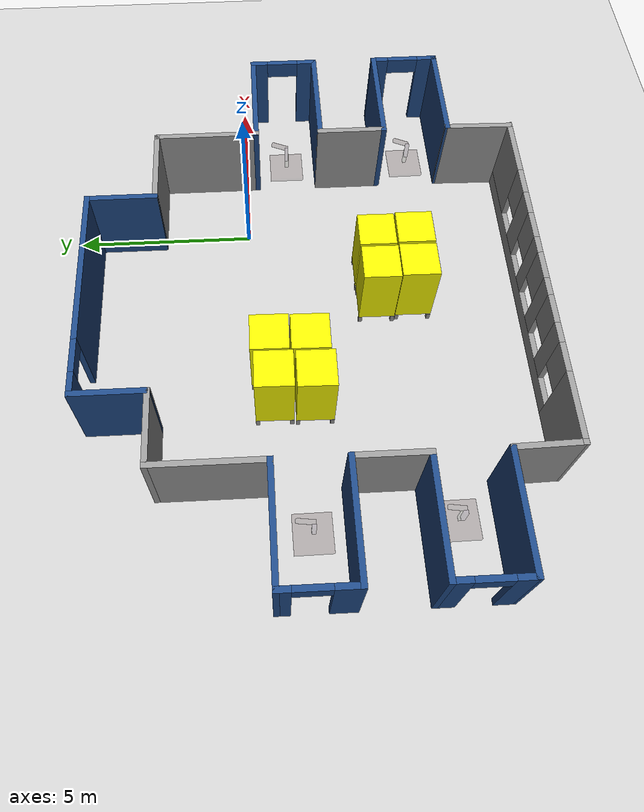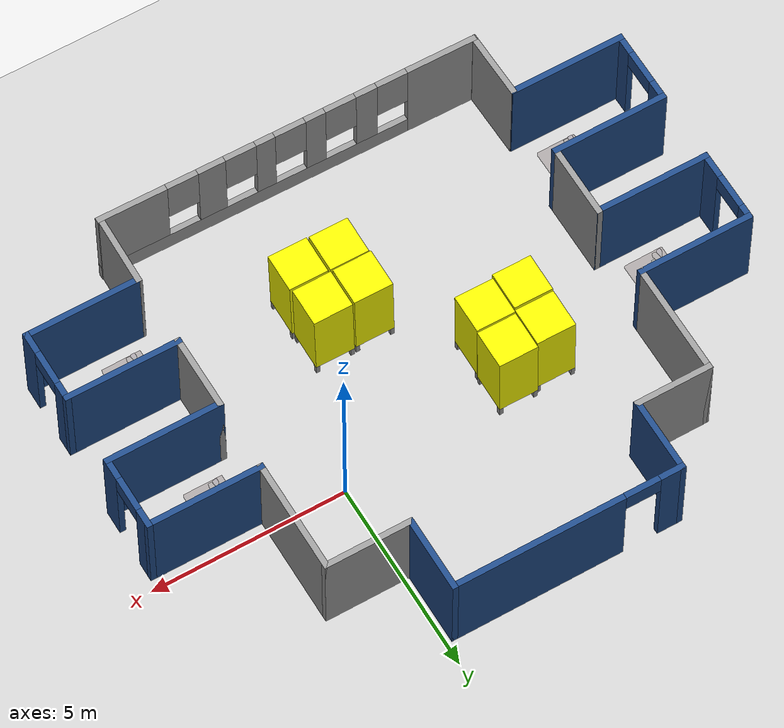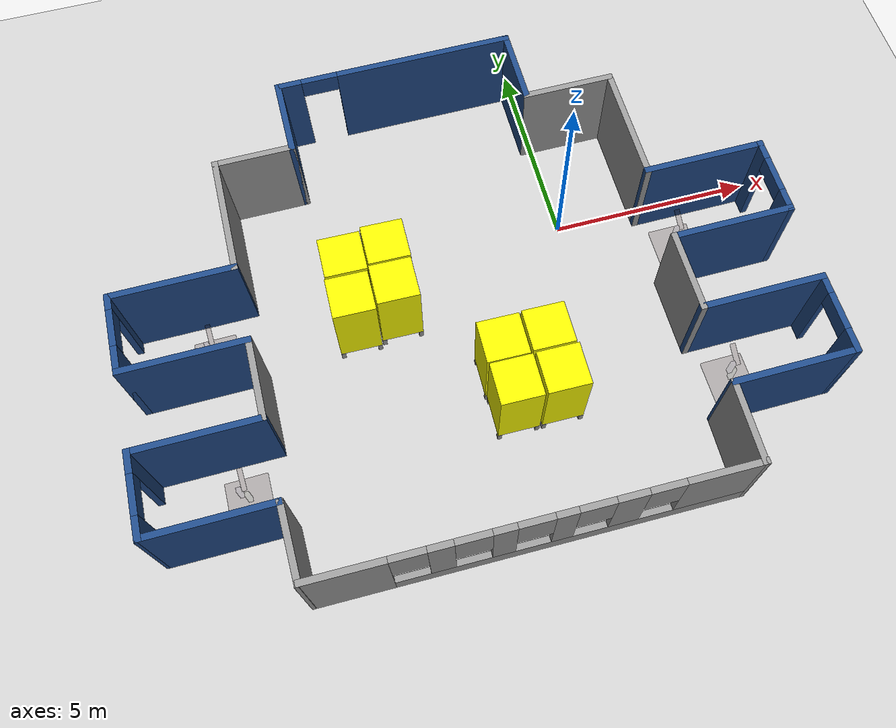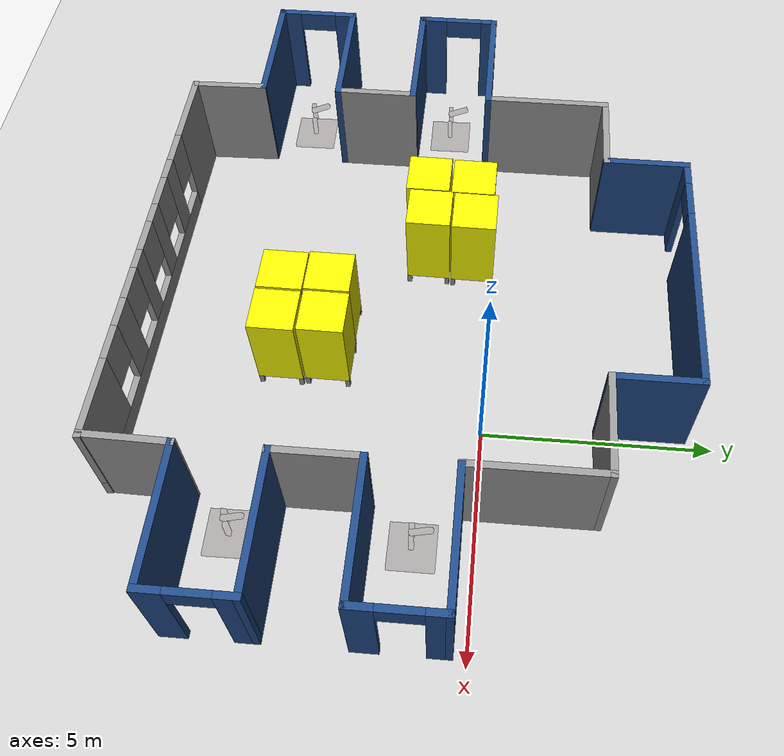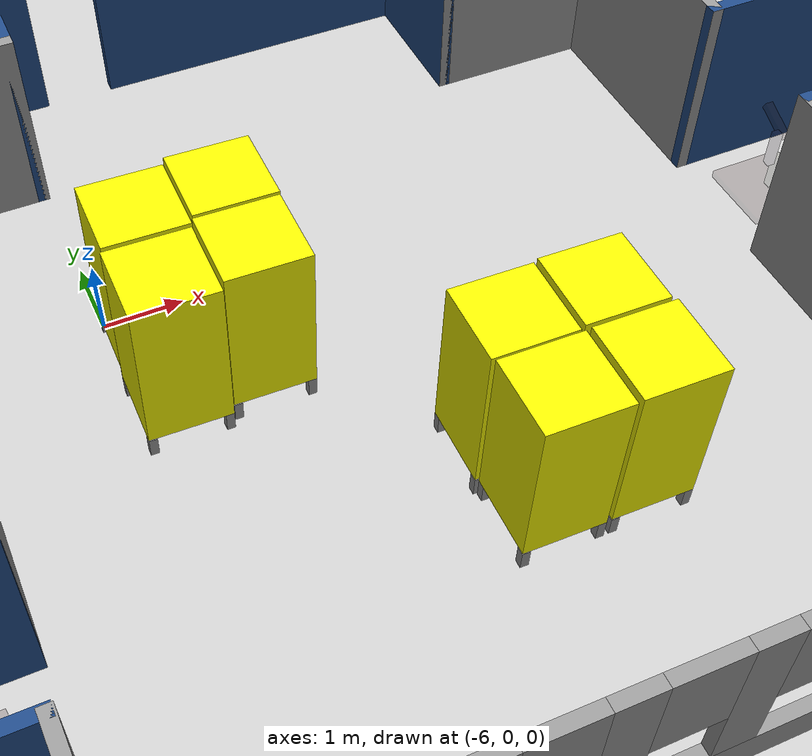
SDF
<sdf version="1.7">
 <world name="default">
  <plugin name="hello" filename="/home/jetson/workspace/ARFloor/build/libhello.so"/>
  <model name="ground_plane">
   <static>1</static>
   <link name="link">
    <collision name="collision">
     <geometry><plane><normal>0 0 1</normal><size>100 100</size></plane></geometry>
     <surface>
      <contact><collide_bitmask>65535</collide_bitmask></contact>
      <friction><ode><mu>100</mu><mu2>50</mu2></ode></friction>
     </surface>
    </collision>
    <visual name="visual">
     <cast_shadows>0</cast_shadows>
     <geometry><plane><normal>0 0 1</normal><size>100 100</size></plane></geometry>
     <material>
      <script><uri>file://media/materials/scripts/gazebo.material</uri><name>Gazebo/Grey</name></script>
     </material>
    </visual>
   </link>
  </model>
  <light name="sun" type="directional">
   <pose>0 0 10 0 -0 0</pose>
   <diffuse>0.8 0.8 0.8 1</diffuse>
   <specular>0.2 0.2 0.2 1</specular>
   <attenuation>
    <range>1000</range>
    <constant>0.9</constant>
    <linear>0.01</linear>
    <quadratic>0.001</quadratic>
   </attenuation>
   <direction>-0.5 0.1 -0.9</direction>
   <spot><inner_angle>0</inner_angle><outer_angle>0</outer_angle><falloff>0</falloff></spot>
  </light>
  <gravity>0 0 -9.8</gravity>
  <magnetic_field>6e-06 2.3e-05 -4.2e-05</magnetic_field>
  <atmosphere type="adiabatic"/>
  <physics type="ode">
   <max_step_size>0.001</max_step_size>
   <real_time_factor>1</real_time_factor>
   <real_time_update_rate>1000</real_time_update_rate>
  </physics>
  <scene><ambient>0.4 0.4 0.4 1</ambient><background>0.7 0.7 0.7 1</background><shadows>1</shadows></scene>
  <spherical_coordinates>
   <surface_model>EARTH_WGS84</surface_model>
   <latitude_deg>0</latitude_deg>
   <longitude_deg>0</longitude_deg>
   <elevation>0</elevation>
   <heading_deg>0</heading_deg>
  </spherical_coordinates>
  <model name="AmazonRoboticsFloor">
   <pose>-2.98765 -1.66162 0 0 -0 0</pose>
   <link name="Wall_1">
    <collision name="Wall_1_Collision">
     <geometry><box><size>3 0.15 2.5</size></box></geometry>
     <pose>0 0 1.25 0 -0 0</pose>
    </collision>
    <visual name="Wall_1_Visual">
     <pose>0 0 1.25 0 -0 0</pose>
     <geometry><box><size>3 0.15 2.5</size></box></geometry>
     <material>
      <script><uri>file://media/materials/scripts/gazebo.material</uri><name>Gazebo/Grey</name></script>
      <ambient>1 1 1 1</ambient>
     </material>
     <meta><layer>0</layer></meta>
    </visual>
    <pose>-4.92496 2.75442 0 0 -0 -1.5708</pose>
   </link>
   <link name="Wall_10">
    <pose>0.03254 -5.97119 0 0 -0 -0.011673</pose>
    <visual name="Wall_10_Visual_0">
     <pose>-4.02993 0 1.25 0 -0 0</pose>
     <geometry><box><size>1.8463 0.15 2.5</size></box></geometry>
     <material>
      <script><uri>file://media/materials/scripts/gazebo.material</uri><name>Gazebo/Grey</name></script>
      <ambient>1 1 1 1</ambient>
     </material>
     <meta><layer>0</layer></meta>
    </visual>
    <collision name="Wall_10_Collision_0">
     <geometry><box><size>1.8463 0.15 2.5</size></box></geometry>
     <pose>-4.02993 0 1.25 0 -0 0</pose>
    </collision>
    <visual name="Wall_10_Visual_1">
     <pose>0.923151 0 0.25 0 -0 0</pose>
     <geometry><box><size>8.05987 0.15 0.5</size></box></geometry>
     <material>
      <script><uri>file://media/materials/scripts/gazebo.material</uri><name>Gazebo/Grey</name></script>
      <ambient>1 1 1 1</ambient>
     </material>
     <meta><layer>0</layer></meta>
    </visual>
    <collision name="Wall_10_Collision_1">
     <geometry><box><size>8.05987 0.15 0.5</size></box></geometry>
     <pose>0.923151 0 0.25 0 -0 0</pose>
    </collision>
    <visual name="Wall_10_Visual_2">
     <pose>-2.02774 0 1.5 0 -0 0</pose>
     <geometry><box><size>0.558079 0.15 2</size></box></geometry>
     <material>
      <script><uri>file://media/materials/scripts/gazebo.material</uri><name>Gazebo/Grey</name></script>
      <ambient>1 1 1 1</ambient>
     </material>
     <meta><layer>0</layer></meta>
    </visual>
    <collision name="Wall_10_Collision_2">
     <geometry><box><size>0.558079 0.15 2</size></box></geometry>
     <pose>-2.02774 0 1.5 0 -0 0</pose>
    </collision>
    <visual name="Wall_10_Visual_3">
     <pose>-0.689635 0 1.5 0 -0 0</pose>
     <geometry><box><size>0.518135 0.15 2</size></box></geometry>
     <material>
      <script><uri>file://media/materials/scripts/gazebo.material</uri><name>Gazebo/Grey</name></script>
      <ambient>1 1 1 1</ambient>
     </material>
     <meta><layer>0</layer></meta>
    </visual>
    <collision name="Wall_10_Collision_3">
     <geometry><box><size>0.518135 0.15 2</size></box></geometry>
     <pose>-0.689635 0 1.5 0 -0 0</pose>
    </collision>
    <visual name="Wall_10_Visual_4">
     <pose>0.616096 0 1.5 0 -0 0</pose>
     <geometry><box><size>0.493327 0.15 2</size></box></geometry>
     <material>
      <script><uri>file://media/materials/scripts/gazebo.material</uri><name>Gazebo/Grey</name></script>
      <ambient>1 1 1 1</ambient>
     </material>
     <meta><layer>0</layer></meta>
    </visual>
    <collision name="Wall_10_Collision_4">
     <geometry><box><size>0.493327 0.15 2</size></box></geometry>
     <pose>0.616096 0 1.5 0 -0 0</pose>
    </collision>
    <visual name="Wall_10_Visual_5">
     <pose>2.01412 0 1.5 0 -0 0</pose>
     <geometry><box><size>0.702718 0.15 2</size></box></geometry>
     <material>
      <script><uri>file://media/materials/scripts/gazebo.material</uri><name>Gazebo/Grey</name></script>
      <ambient>1 1 1 1</ambient>
     </material>
     <meta><layer>0</layer></meta>
    </visual>
    <collision name="Wall_10_Collision_5">
     <geometry><box><size>0.702718 0.15 2</size></box></geometry>
     <pose>2.01412 0 1.5 0 -0 0</pose>
    </collision>
    <visual name="Wall_10_Visual_6">
     <pose>4.05928 0 1.5 0 -0 0</pose>
     <geometry><box><size>1.78761 0.15 2</size></box></geometry>
     <material>
      <script><uri>file://media/materials/scripts/gazebo.material</uri><name>Gazebo/Grey</name></script>
      <ambient>1 1 1 1</ambient>
     </material>
     <meta><layer>0</layer></meta>
    </visual>
    <collision name="Wall_10_Collision_6">
     <geometry><box><size>1.78761 0.15 2</size></box></geometry>
     <pose>4.05928 0 1.5 0 -0 0</pose>
    </collision>
    <visual name="Wall_10_Visual_7">
     <pose>-2.70678 0 1.9 0 -0 0</pose>
     <geometry><box><size>0.8 0.15 1.2</size></box></geometry>
     <material>
      <script><uri>file://media/materials/scripts/gazebo.material</uri><name>Gazebo/Grey</name></script>
      <ambient>1 1 1 1</ambient>
     </material>
     <meta><layer>0</layer></meta>
    </visual>
    <collision name="Wall_10_Collision_7">
     <geometry><box><size>0.8 0.15 1.2</size></box></geometry>
     <pose>-2.70678 0 1.9 0 -0 0</pose>
    </collision>
    <visual name="Wall_10_Visual_8">
     <pose>-1.3487 0 1.9 0 -0 0</pose>
     <geometry><box><size>0.8 0.15 1.2</size></box></geometry>
     <material>
      <script><uri>file://media/materials/scripts/gazebo.material</uri><name>Gazebo/Grey</name></script>
      <ambient>1 1 1 1</ambient>
     </material>
     <meta><layer>0</layer></meta>
    </visual>
    <collision name="Wall_10_Collision_8">
     <geometry><box><size>0.8 0.15 1.2</size></box></geometry>
     <pose>-1.3487 0 1.9 0 -0 0</pose>
    </collision>
    <visual name="Wall_10_Visual_9">
     <pose>-0.030567 0 1.9 0 -0 0</pose>
     <geometry><box><size>0.8 0.15 1.2</size></box></geometry>
     <material>
      <script><uri>file://media/materials/scripts/gazebo.material</uri><name>Gazebo/Grey</name></script>
      <ambient>1 1 1 1</ambient>
     </material>
     <meta><layer>0</layer></meta>
    </visual>
    <collision name="Wall_10_Collision_9">
     <geometry><box><size>0.8 0.15 1.2</size></box></geometry>
     <pose>-0.030567 0 1.9 0 -0 0</pose>
    </collision>
    <visual name="Wall_10_Visual_10">
     <pose>1.26276 0 1.9 0 -0 0</pose>
     <geometry><box><size>0.8 0.15 1.2</size></box></geometry>
     <material>
      <script><uri>file://media/materials/scripts/gazebo.material</uri><name>Gazebo/Grey</name></script>
      <ambient>1 1 1 1</ambient>
     </material>
     <meta><layer>0</layer></meta>
    </visual>
    <collision name="Wall_10_Collision_10">
     <geometry><box><size>0.8 0.15 1.2</size></box></geometry>
     <pose>1.26276 0 1.9 0 -0 0</pose>
    </collision>
    <visual name="Wall_10_Visual_11">
     <pose>2.76548 0 1.9 0 -0 0</pose>
     <geometry><box><size>0.8 0.15 1.2</size></box></geometry>
     <material>
      <script><uri>file://media/materials/scripts/gazebo.material</uri><name>Gazebo/Grey</name></script>
      <ambient>1 1 1 1</ambient>
     </material>
     <meta><layer>0</layer></meta>
    </visual>
    <collision name="Wall_10_Collision_11">
     <geometry><box><size>0.8 0.15 1.2</size></box></geometry>
     <pose>2.76548 0 1.9 0 -0 0</pose>
    </collision>
   </link>
   <link name="Wall_12">
    <collision name="Wall_12_Collision">
     <geometry><box><size>3 0.15 2.5</size></box></geometry>
     <pose>0 0 1.25 0 -0 0</pose>
    </collision>
    <visual name="Wall_12_Visual">
     <pose>0 0 1.25 0 -0 0</pose>
     <geometry><box><size>3 0.15 2.5</size></box></geometry>
     <material>
      <script><uri>file://media/materials/scripts/gazebo.material</uri><name>Gazebo/Grey</name></script>
      <ambient>0.12549 0.290196 0.529412 1</ambient>
     </material>
     <meta><layer>0</layer></meta>
    </visual>
    <pose>6.35004 -4.22058 0 0 -0 0</pose>
   </link>
   <link name="Wall_13">
    <pose>7.77504 -3.29558 0 0 -0 1.5708</pose>
    <visual name="Wall_13_Visual_0">
     <pose>-0.706177 0 1.25 0 -0 0</pose>
     <geometry><box><size>0.587646 0.15 2.5</size></box></geometry>
     <material>
      <script><uri>file://media/materials/scripts/gazebo.material</uri><name>Gazebo/Grey</name></script>
      <ambient>0.12549 0.290196 0.529412 1</ambient>
     </material>
     <meta><layer>0</layer></meta>
    </visual>
    <collision name="Wall_13_Collision_0">
     <geometry><box><size>0.587646 0.15 2.5</size></box></geometry>
     <pose>-0.706177 0 1.25 0 -0 0</pose>
    </collision>
    <visual name="Wall_13_Visual_1">
     <pose>0.743823 0 1.25 0 -0 0</pose>
     <geometry><box><size>0.512354 0.15 2.5</size></box></geometry>
     <material>
      <script><uri>file://media/materials/scripts/gazebo.material</uri><name>Gazebo/Grey</name></script>
      <ambient>0.12549 0.290196 0.529412 1</ambient>
     </material>
     <meta><layer>0</layer></meta>
    </visual>
    <collision name="Wall_13_Collision_1">
     <geometry><box><size>0.512354 0.15 2.5</size></box></geometry>
     <pose>0.743823 0 1.25 0 -0 0</pose>
    </collision>
    <visual name="Wall_13_Visual_2">
     <pose>0.037646 0 2.25 0 -0 0</pose>
     <geometry><box><size>0.9 0.15 0.5</size></box></geometry>
     <material>
      <script><uri>file://media/materials/scripts/gazebo.material</uri><name>Gazebo/Grey</name></script>
      <ambient>0.12549 0.290196 0.529412 1</ambient>
     </material>
     <meta><layer>0</layer></meta>
    </visual>
    <collision name="Wall_13_Collision_2">
     <geometry><box><size>0.9 0.15 0.5</size></box></geometry>
     <pose>0.037646 0 2.25 0 -0 0</pose>
    </collision>
   </link>
   <link name="Wall_14">
    <collision name="Wall_14_Collision">
     <geometry><box><size>3 0.15 2.5</size></box></geometry>
     <pose>0 0 1.25 0 -0 0</pose>
    </collision>
    <visual name="Wall_14_Visual">
     <pose>0 0 1.25 0 -0 0</pose>
     <geometry><box><size>3 0.15 2.5</size></box></geometry>
     <material>
      <script><uri>file://media/materials/scripts/gazebo.material</uri><name>Gazebo/Grey</name></script>
      <ambient>0.12549 0.290196 0.529412 1</ambient>
     </material>
     <meta><layer>0</layer></meta>
    </visual>
    <pose>6.35004 -2.37058 0 0 -0 3.14159</pose>
   </link>
   <link name="Wall_15">
    <collision name="Wall_15_Collision">
     <geometry><box><size>2 0.15 2.5</size></box></geometry>
     <pose>0 0 1.25 0 -0 0</pose>
    </collision>
    <visual name="Wall_15_Visual">
     <pose>0 0 1.25 0 -0 0</pose>
     <geometry><box><size>2 0.15 2.5</size></box></geometry>
     <material>
      <script><uri>file://media/materials/scripts/gazebo.material</uri><name>Gazebo/Grey</name></script>
      <ambient>1 1 1 1</ambient>
     </material>
     <meta><layer>0</layer></meta>
    </visual>
    <pose>4.92504 -1.44558 0 0 -0 1.5708</pose>
   </link>
   <link name="Wall_17">
    <collision name="Wall_17_Collision">
     <geometry><box><size>3 0.15 2.5</size></box></geometry>
     <pose>0 0 1.25 0 -0 0</pose>
    </collision>
    <visual name="Wall_17_Visual">
     <pose>0 0 1.25 0 -0 0</pose>
     <geometry><box><size>3 0.15 2.5</size></box></geometry>
     <material>
      <script><uri>file://media/materials/scripts/gazebo.material</uri><name>Gazebo/Grey</name></script>
      <ambient>0.12549 0.290196 0.529412 1</ambient>
     </material>
     <meta><layer>0</layer></meta>
    </visual>
    <pose>6.35004 -0.52058 0 0 -0 0</pose>
   </link>
   <link name="Wall_18">
    <pose>7.77504 0.40442 0 0 -0 1.5708</pose>
    <visual name="Wall_18_Visual_0">
     <pose>-0.704677 0 1.25 0 -0 0</pose>
     <geometry><box><size>0.590647 0.15 2.5</size></box></geometry>
     <material>
      <script><uri>file://media/materials/scripts/gazebo.material</uri><name>Gazebo/Grey</name></script>
      <ambient>0.12549 0.290196 0.529412 1</ambient>
     </material>
     <meta><layer>0</layer></meta>
    </visual>
    <collision name="Wall_18_Collision_0">
     <geometry><box><size>0.590647 0.15 2.5</size></box></geometry>
     <pose>-0.704677 0 1.25 0 -0 0</pose>
    </collision>
    <visual name="Wall_18_Visual_1">
     <pose>0.745323 0 1.25 0 -0 0</pose>
     <geometry><box><size>0.509353 0.15 2.5</size></box></geometry>
     <material>
      <script><uri>file://media/materials/scripts/gazebo.material</uri><name>Gazebo/Grey</name></script>
      <ambient>0.12549 0.290196 0.529412 1</ambient>
     </material>
     <meta><layer>0</layer></meta>
    </visual>
    <collision name="Wall_18_Collision_1">
     <geometry><box><size>0.509353 0.15 2.5</size></box></geometry>
     <pose>0.745323 0 1.25 0 -0 0</pose>
    </collision>
    <visual name="Wall_18_Visual_2">
     <pose>0.040647 0 2.25 0 -0 0</pose>
     <geometry><box><size>0.9 0.15 0.5</size></box></geometry>
     <material>
      <script><uri>file://media/materials/scripts/gazebo.material</uri><name>Gazebo/Grey</name></script>
      <ambient>0.12549 0.290196 0.529412 1</ambient>
     </material>
     <meta><layer>0</layer></meta>
    </visual>
    <collision name="Wall_18_Collision_2">
     <geometry><box><size>0.9 0.15 0.5</size></box></geometry>
     <pose>0.040647 0 2.25 0 -0 0</pose>
    </collision>
   </link>
   <link name="Wall_19">
    <collision name="Wall_19_Collision">
     <geometry><box><size>3 0.15 2.5</size></box></geometry>
     <pose>0 0 1.25 0 -0 0</pose>
    </collision>
    <visual name="Wall_19_Visual">
     <pose>0 0 1.25 0 -0 0</pose>
     <geometry><box><size>3 0.15 2.5</size></box></geometry>
     <material>
      <script><uri>file://media/materials/scripts/gazebo.material</uri><name>Gazebo/Grey</name></script>
      <ambient>0.12549 0.290196 0.529412 1</ambient>
     </material>
     <meta><layer>0</layer></meta>
    </visual>
    <pose>6.35004 1.32942 0 0 -0 3.14159</pose>
   </link>
   <link name="Wall_2">
    <collision name="Wall_2_Collision">
     <geometry><box><size>3 0.15 2.5</size></box></geometry>
     <pose>0 0 1.25 0 -0 0</pose>
    </collision>
    <visual name="Wall_2_Visual">
     <pose>0 0 1.25 0 -0 0</pose>
     <geometry><box><size>3 0.15 2.5</size></box></geometry>
     <material>
      <script><uri>file://media/materials/scripts/gazebo.material</uri><name>Gazebo/Grey</name></script>
      <ambient>0.12549 0.290196 0.529412 1</ambient>
     </material>
     <meta><layer>0</layer></meta>
    </visual>
    <pose>-6.34996 1.32942 0 0 -0 3.14159</pose>
   </link>
   <link name="Wall_20">
    <collision name="Wall_20_Collision">
     <geometry><box><size>3 0.15 2.5</size></box></geometry>
     <pose>0 0 1.25 0 -0 0</pose>
    </collision>
    <visual name="Wall_20_Visual">
     <pose>0 0 1.25 0 -0 0</pose>
     <geometry><box><size>3 0.15 2.5</size></box></geometry>
     <material>
      <script><uri>file://media/materials/scripts/gazebo.material</uri><name>Gazebo/Grey</name></script>
      <ambient>1 1 1 1</ambient>
     </material>
     <meta><layer>0</layer></meta>
    </visual>
    <pose>4.92504 2.75442 0 0 -0 1.5708</pose>
   </link>
   <link name="Wall_22">
    <collision name="Wall_22_Collision">
     <geometry><box><size>2 0.15 2.5</size></box></geometry>
     <pose>0 0 1.25 0 -0 0</pose>
    </collision>
    <visual name="Wall_22_Visual">
     <pose>0 0 1.25 0 -0 0</pose>
     <geometry><box><size>2 0.15 2.5</size></box></geometry>
     <material>
      <script><uri>file://media/materials/scripts/gazebo.material</uri><name>Gazebo/Grey</name></script>
      <ambient>1 1 1 1</ambient>
     </material>
     <meta><layer>0</layer></meta>
    </visual>
    <pose>-3.99996 4.17942 0 0 -0 0</pose>
   </link>
   <link name="Wall_24">
    <collision name="Wall_24_Collision">
     <geometry><box><size>2 0.15 2.5</size></box></geometry>
     <pose>0 0 1.25 0 -0 0</pose>
    </collision>
    <visual name="Wall_24_Visual">
     <pose>0 0 1.25 0 -0 0</pose>
     <geometry><box><size>2 0.15 2.5</size></box></geometry>
     <material>
      <script><uri>file://media/materials/scripts/gazebo.material</uri><name>Gazebo/Grey</name></script>
      <ambient>0.12549 0.290196 0.529412 1</ambient>
     </material>
     <meta><layer>0</layer></meta>
    </visual>
    <pose>-3.07496 5.10442 0 0 -0 1.5708</pose>
   </link>
   <link name="Wall_25">
    <pose>-0.149958 6.02942 0 0 -0 0</pose>
    <visual name="Wall_25_Visual_0">
     <pose>-2.67362 0 1.25 0 -0 0</pose>
     <geometry><box><size>0.652756 0.15 2.5</size></box></geometry>
     <material>
      <script><uri>file://media/materials/scripts/gazebo.material</uri><name>Gazebo/Grey</name></script>
      <ambient>0.12549 0.290196 0.529412 1</ambient>
     </material>
     <meta><layer>0</layer></meta>
    </visual>
    <collision name="Wall_25_Collision_0">
     <geometry><box><size>0.652756 0.15 2.5</size></box></geometry>
     <pose>-2.67362 0 1.25 0 -0 0</pose>
    </collision>
    <visual name="Wall_25_Visual_1">
     <pose>0.776378 0 1.25 0 -0 0</pose>
     <geometry><box><size>4.44724 0.15 2.5</size></box></geometry>
     <material>
      <script><uri>file://media/materials/scripts/gazebo.material</uri><name>Gazebo/Grey</name></script>
      <ambient>0.12549 0.290196 0.529412 1</ambient>
     </material>
     <meta><layer>0</layer></meta>
    </visual>
    <collision name="Wall_25_Collision_1">
     <geometry><box><size>4.44724 0.15 2.5</size></box></geometry>
     <pose>0.776378 0 1.25 0 -0 0</pose>
    </collision>
    <visual name="Wall_25_Visual_2">
     <pose>-1.89724 0 2.25 0 -0 0</pose>
     <geometry><box><size>0.9 0.15 0.5</size></box></geometry>
     <material>
      <script><uri>file://media/materials/scripts/gazebo.material</uri><name>Gazebo/Grey</name></script>
      <ambient>0.12549 0.290196 0.529412 1</ambient>
     </material>
     <meta><layer>0</layer></meta>
    </visual>
    <collision name="Wall_25_Collision_2">
     <geometry><box><size>0.9 0.15 0.5</size></box></geometry>
     <pose>-1.89724 0 2.25 0 -0 0</pose>
    </collision>
   </link>
   <link name="Wall_29">
    <collision name="Wall_29_Collision">
     <geometry><box><size>2 0.15 2.5</size></box></geometry>
     <pose>0 0 1.25 0 -0 0</pose>
    </collision>
    <visual name="Wall_29_Visual">
     <pose>0 0 1.25 0 -0 0</pose>
     <geometry><box><size>2 0.15 2.5</size></box></geometry>
     <material>
      <script><uri>file://media/materials/scripts/gazebo.material</uri><name>Gazebo/Grey</name></script>
      <ambient>0.12549 0.290196 0.529412 1</ambient>
     </material>
     <meta><layer>0</layer></meta>
    </visual>
    <pose>2.77504 5.10442 0 0 -0 -1.5708</pose>
   </link>
   <link name="Wall_3">
    <pose>-7.77496 0.40442 0 0 -0 -1.5708</pose>
    <visual name="Wall_3_Visual_0">
     <pose>-0.798223 0 1.25 0 -0 0</pose>
     <geometry><box><size>0.403554 0.15 2.5</size></box></geometry>
     <material>
      <script><uri>file://media/materials/scripts/gazebo.material</uri><name>Gazebo/Grey</name></script>
      <ambient>0.12549 0.290196 0.529412 1</ambient>
     </material>
     <meta><layer>0</layer></meta>
    </visual>
    <collision name="Wall_3_Collision_0">
     <geometry><box><size>0.403554 0.15 2.5</size></box></geometry>
     <pose>-0.798223 0 1.25 0 -0 0</pose>
    </collision>
    <visual name="Wall_3_Visual_1">
     <pose>0.651777 0 1.25 0 -0 0</pose>
     <geometry><box><size>0.696446 0.15 2.5</size></box></geometry>
     <material>
      <script><uri>file://media/materials/scripts/gazebo.material</uri><name>Gazebo/Grey</name></script>
      <ambient>0.12549 0.290196 0.529412 1</ambient>
     </material>
     <meta><layer>0</layer></meta>
    </visual>
    <collision name="Wall_3_Collision_1">
     <geometry><box><size>0.696446 0.15 2.5</size></box></geometry>
     <pose>0.651777 0 1.25 0 -0 0</pose>
    </collision>
    <visual name="Wall_3_Visual_2">
     <pose>-0.146446 0 2.25 0 -0 0</pose>
     <geometry><box><size>0.9 0.15 0.5</size></box></geometry>
     <material>
      <script><uri>file://media/materials/scripts/gazebo.material</uri><name>Gazebo/Grey</name></script>
      <ambient>0.12549 0.290196 0.529412 1</ambient>
     </material>
     <meta><layer>0</layer></meta>
    </visual>
    <collision name="Wall_3_Collision_2">
     <geometry><box><size>0.9 0.15 0.5</size></box></geometry>
     <pose>-0.146446 0 2.25 0 -0 0</pose>
    </collision>
   </link>
   <link name="Wall_30">
    <collision name="Wall_30_Collision">
     <geometry><box><size>2.3 0.15 2.5</size></box></geometry>
     <pose>0 0 1.25 0 -0 0</pose>
    </collision>
    <visual name="Wall_30_Visual">
     <pose>0 0 1.25 0 -0 0</pose>
     <geometry><box><size>2.3 0.15 2.5</size></box></geometry>
     <material>
      <script><uri>file://media/materials/scripts/gazebo.material</uri><name>Gazebo/Grey</name></script>
      <ambient>1 1 1 1</ambient>
     </material>
     <meta><layer>0</layer></meta>
    </visual>
    <pose>3.85004 4.17942 0 0 -0 0</pose>
   </link>
   <link name="Wall_34">
    <collision name="Wall_34_Collision">
     <geometry><box><size>1.82164 0.15 2.5</size></box></geometry>
     <pose>0 0 1.25 0 -0 0</pose>
    </collision>
    <visual name="Wall_34_Visual">
     <pose>0 0 1.25 0 -0 0</pose>
     <geometry><box><size>1.82164 0.15 2.5</size></box></geometry>
     <material>
      <script><uri>file://media/materials/scripts/gazebo.material</uri><name>Gazebo/Grey</name></script>
      <ambient>1 1 1 1</ambient>
     </material>
     <meta><layer>0</layer></meta>
    </visual>
    <pose>-4.88509 -5.07896 0 0 -0 -1.54693</pose>
   </link>
   <link name="Wall_35">
    <collision name="Wall_35_Collision">
     <geometry><box><size>0.15 0.15 2.5</size></box></geometry>
     <pose>0 0 1.25 0 -0 0</pose>
    </collision>
    <visual name="Wall_35_Visual">
     <pose>0 0 1.25 0 -0 0</pose>
     <geometry><box><size>0.15 0.15 2.5</size></box></geometry>
     <material>
      <script><uri>file://media/materials/scripts/gazebo.material</uri><name>Gazebo/Grey</name></script>
      <ambient>1 1 1 1</ambient>
     </material>
     <meta><layer>0</layer></meta>
    </visual>
    <pose>-4.86515 -5.91425 0 0 -0 0</pose>
   </link>
   <link name="Wall_37">
    <collision name="Wall_37_Collision">
     <geometry><box><size>1.95761 0.15 2.5</size></box></geometry>
     <pose>0 0 1.25 0 -0 0</pose>
    </collision>
    <visual name="Wall_37_Visual">
     <pose>0 0 1.25 0 -0 0</pose>
     <geometry><box><size>1.95761 0.15 2.5</size></box></geometry>
     <material>
      <script><uri>file://media/materials/scripts/gazebo.material</uri><name>Gazebo/Grey</name></script>
      <ambient>1 1 1 1</ambient>
     </material>
     <meta><layer>0</layer></meta>
    </visual>
    <pose>4.9077 -5.12436 0 0 -0 1.55161</pose>
   </link>
   <link name="Wall_4">
    <collision name="Wall_4_Collision">
     <geometry><box><size>3 0.15 2.5</size></box></geometry>
     <pose>0 0 1.25 0 -0 0</pose>
    </collision>
    <visual name="Wall_4_Visual">
     <pose>0 0 1.25 0 -0 0</pose>
     <geometry><box><size>3 0.15 2.5</size></box></geometry>
     <material>
      <script><uri>file://media/materials/scripts/gazebo.material</uri><name>Gazebo/Grey</name></script>
      <ambient>0.12549 0.290196 0.529412 1</ambient>
     </material>
     <meta><layer>0</layer></meta>
    </visual>
    <pose>-6.34996 -0.52058 0 0 -0 0</pose>
   </link>
   <link name="Wall_5">
    <collision name="Wall_5_Collision">
     <geometry><box><size>2 0.15 2.5</size></box></geometry>
     <pose>0 0 1.25 0 -0 0</pose>
    </collision>
    <visual name="Wall_5_Visual">
     <pose>0 0 1.25 0 -0 0</pose>
     <geometry><box><size>2 0.15 2.5</size></box></geometry>
     <material>
      <script><uri>file://media/materials/scripts/gazebo.material</uri><name>Gazebo/Grey</name></script>
      <ambient>1 1 1 1</ambient>
     </material>
     <meta><layer>0</layer></meta>
    </visual>
    <pose>-4.92496 -1.44558 0 0 -0 -1.5708</pose>
   </link>
   <link name="Wall_6">
    <collision name="Wall_6_Collision">
     <geometry><box><size>3 0.15 2.5</size></box></geometry>
     <pose>0 0 1.25 0 -0 0</pose>
    </collision>
    <visual name="Wall_6_Visual">
     <pose>0 0 1.25 0 -0 0</pose>
     <geometry><box><size>3 0.15 2.5</size></box></geometry>
     <material>
      <script><uri>file://media/materials/scripts/gazebo.material</uri><name>Gazebo/Grey</name></script>
      <ambient>0.12549 0.290196 0.529412 1</ambient>
     </material>
     <meta><layer>0</layer></meta>
    </visual>
    <pose>-6.34996 -2.37058 0 0 -0 3.14159</pose>
   </link>
   <link name="Wall_7">
    <pose>-7.77496 -3.29558 0 0 -0 -1.5708</pose>
    <visual name="Wall_7_Visual_0">
     <pose>-0.72619 0 1.25 0 -0 0</pose>
     <geometry><box><size>0.54762 0.15 2.5</size></box></geometry>
     <material>
      <script><uri>file://media/materials/scripts/gazebo.material</uri><name>Gazebo/Grey</name></script>
      <ambient>0.12549 0.290196 0.529412 1</ambient>
     </material>
     <meta><layer>0</layer></meta>
    </visual>
    <collision name="Wall_7_Collision_0">
     <geometry><box><size>0.54762 0.15 2.5</size></box></geometry>
     <pose>-0.72619 0 1.25 0 -0 0</pose>
    </collision>
    <visual name="Wall_7_Visual_1">
     <pose>0.72381 0 1.25 0 -0 0</pose>
     <geometry><box><size>0.55238 0.15 2.5</size></box></geometry>
     <material>
      <script><uri>file://media/materials/scripts/gazebo.material</uri><name>Gazebo/Grey</name></script>
      <ambient>0.12549 0.290196 0.529412 1</ambient>
     </material>
     <meta><layer>0</layer></meta>
    </visual>
    <collision name="Wall_7_Collision_1">
     <geometry><box><size>0.55238 0.15 2.5</size></box></geometry>
     <pose>0.72381 0 1.25 0 -0 0</pose>
    </collision>
    <visual name="Wall_7_Visual_2">
     <pose>-0.00238 0 2.25 0 -0 0</pose>
     <geometry><box><size>0.9 0.15 0.5</size></box></geometry>
     <material>
      <script><uri>file://media/materials/scripts/gazebo.material</uri><name>Gazebo/Grey</name></script>
      <ambient>0.12549 0.290196 0.529412 1</ambient>
     </material>
     <meta><layer>0</layer></meta>
    </visual>
    <collision name="Wall_7_Collision_2">
     <geometry><box><size>0.9 0.15 0.5</size></box></geometry>
     <pose>-0.00238 0 2.25 0 -0 0</pose>
    </collision>
   </link>
   <link name="Wall_8">
    <collision name="Wall_8_Collision">
     <geometry><box><size>3 0.15 2.5</size></box></geometry>
     <pose>0 0 1.25 0 -0 0</pose>
    </collision>
    <visual name="Wall_8_Visual">
     <pose>0 0 1.25 0 -0 0</pose>
     <geometry><box><size>3 0.15 2.5</size></box></geometry>
     <material>
      <script><uri>file://media/materials/scripts/gazebo.material</uri><name>Gazebo/Grey</name></script>
      <ambient>0.12549 0.290196 0.529412 1</ambient>
     </material>
     <meta><layer>0</layer></meta>
    </visual>
    <pose>-6.34996 -4.22216 0 0 -0 -0.001109</pose>
   </link>
   <static>1</static>
  </model>
  <model name="StoragePod">
   <link name="link_2">
    <inertial>
     <mass>1</mass>
     <inertia>
      <ixx>0.166667</ixx>
      <ixy>0</ixy>
      <ixz>0</ixz>
      <iyy>0.166667</iyy>
      <iyz>0</iyz>
      <izz>0.166667</izz>
     </inertia>
    </inertial>
    <pose>-0.45 -0.45 -0.237 0 -0 0</pose>
    <visual name="visual">
     <geometry><box><size>0.1 0.1 0.25</size></box></geometry>
     <material>
      <lighting>1</lighting>
      <script><uri>file://media/materials/scripts/gazebo.material</uri><name>Gazebo/Grey</name></script>
      <shader type="pixel"><normal_map>__default__</normal_map></shader>
      <ambient>0.3 0.3 0.3 1</ambient>
      <diffuse>0.7 0.7 0.7 1</diffuse>
      <specular>0.01 0.01 0.01 1</specular>
      <emissive>0 0 0 1</emissive>
     </material>
    </visual>
    <collision name="collision">
     <geometry><box><size>0.1 0.1 0.25</size></box></geometry>
     <surface>
      <friction>
       <ode><mu>1</mu><mu2>1</mu2><fdir1>0 0 0</fdir1><slip1>0</slip1><slip2>0</slip2></ode>
       <torsional>
        <coefficient>1</coefficient>
        <patch_radius>0</patch_radius>
        <surface_radius>0</surface_radius>
        <use_patch_radius>1</use_patch_radius>
        <ode><slip>0</slip></ode>
       </torsional>
      </friction>
      <bounce><restitution_coefficient>0</restitution_coefficient><threshold>1e+06</threshold></bounce>
      <contact>
       <collide_without_contact>0</collide_without_contact>
       <collide_without_contact_bitmask>1</collide_without_contact_bitmask>
       <collide_bitmask>1</collide_bitmask>
       <ode>
        <soft_cfm>0</soft_cfm>
        <soft_erp>0.2</soft_erp>
        <kp>1e+13</kp>
        <kd>1</kd>
        <max_vel>0.01</max_vel>
        <min_depth>0</min_depth>
       </ode>
       <bullet>
        <split_impulse>1</split_impulse>
        <split_impulse_penetration_threshold>-0.01</split_impulse_penetration_threshold>
        <soft_cfm>0</soft_cfm>
        <soft_erp>0.2</soft_erp>
        <kp>1e+13</kp>
        <kd>1</kd>
       </bullet>
      </contact>
     </surface>
    </collision>
   </link>
   <link name="link_2_clone">
    <inertial>
     <mass>1</mass>
     <inertia>
      <ixx>0.166667</ixx>
      <ixy>0</ixy>
      <ixz>0</ixz>
      <iyy>0.166667</iyy>
      <iyz>0</iyz>
      <izz>0.166667</izz>
     </inertia>
    </inertial>
    <pose>0.45 0.45 -0.222 0 -0 0</pose>
    <visual name="visual">
     <geometry><box><size>0.1 0.1 0.25</size></box></geometry>
     <material>
      <lighting>1</lighting>
      <script><uri>file://media/materials/scripts/gazebo.material</uri><name>Gazebo/Grey</name></script>
      <shader type="pixel"><normal_map>__default__</normal_map></shader>
      <ambient>0.3 0.3 0.3 1</ambient>
      <diffuse>0.7 0.7 0.7 1</diffuse>
      <specular>0.01 0.01 0.01 1</specular>
      <emissive>0 0 0 1</emissive>
     </material>
    </visual>
    <collision name="collision">
     <geometry><box><size>0.1 0.1 0.25</size></box></geometry>
     <surface>
      <friction>
       <ode><mu>1</mu><mu2>1</mu2><fdir1>0 0 0</fdir1><slip1>0</slip1><slip2>0</slip2></ode>
       <torsional>
        <coefficient>1</coefficient>
        <patch_radius>0</patch_radius>
        <surface_radius>0</surface_radius>
        <use_patch_radius>1</use_patch_radius>
        <ode><slip>0</slip></ode>
       </torsional>
      </friction>
      <bounce><restitution_coefficient>0</restitution_coefficient><threshold>1e+06</threshold></bounce>
      <contact>
       <collide_without_contact>0</collide_without_contact>
       <collide_without_contact_bitmask>1</collide_without_contact_bitmask>
       <collide_bitmask>1</collide_bitmask>
       <ode>
        <soft_cfm>0</soft_cfm>
        <soft_erp>0.2</soft_erp>
        <kp>1e+13</kp>
        <kd>1</kd>
        <max_vel>0.01</max_vel>
        <min_depth>0</min_depth>
       </ode>
       <bullet>
        <split_impulse>1</split_impulse>
        <split_impulse_penetration_threshold>-0.01</split_impulse_penetration_threshold>
        <soft_cfm>0</soft_cfm>
        <soft_erp>0.2</soft_erp>
        <kp>1e+13</kp>
        <kd>1</kd>
       </bullet>
      </contact>
     </surface>
    </collision>
   </link>
   <link name="link_2_clone_0">
    <inertial>
     <mass>1</mass>
     <inertia>
      <ixx>0.166667</ixx>
      <ixy>0</ixy>
      <ixz>0</ixz>
      <iyy>0.166667</iyy>
      <iyz>0</iyz>
      <izz>0.166667</izz>
     </inertia>
    </inertial>
    <pose>0.45 -0.45 -0.222 0 -0 0</pose>
    <visual name="visual">
     <geometry><box><size>0.1 0.1 0.25</size></box></geometry>
     <material>
      <lighting>1</lighting>
      <script><uri>file://media/materials/scripts/gazebo.material</uri><name>Gazebo/Grey</name></script>
      <shader type="pixel"><normal_map>__default__</normal_map></shader>
      <ambient>0.3 0.3 0.3 1</ambient>
      <diffuse>0.7 0.7 0.7 1</diffuse>
      <specular>0.01 0.01 0.01 1</specular>
      <emissive>0 0 0 1</emissive>
     </material>
    </visual>
    <collision name="collision">
     <geometry><box><size>0.1 0.1 0.25</size></box></geometry>
     <surface>
      <friction>
       <ode><mu>1</mu><mu2>1</mu2><fdir1>0 0 0</fdir1><slip1>0</slip1><slip2>0</slip2></ode>
       <torsional>
        <coefficient>1</coefficient>
        <patch_radius>0</patch_radius>
        <surface_radius>0</surface_radius>
        <use_patch_radius>1</use_patch_radius>
        <ode><slip>0</slip></ode>
       </torsional>
      </friction>
      <bounce><restitution_coefficient>0</restitution_coefficient><threshold>1e+06</threshold></bounce>
      <contact>
       <collide_without_contact>0</collide_without_contact>
       <collide_without_contact_bitmask>1</collide_without_contact_bitmask>
       <collide_bitmask>1</collide_bitmask>
       <ode>
        <soft_cfm>0</soft_cfm>
        <soft_erp>0.2</soft_erp>
        <kp>1e+13</kp>
        <kd>1</kd>
        <max_vel>0.01</max_vel>
        <min_depth>0</min_depth>
       </ode>
       <bullet>
        <split_impulse>1</split_impulse>
        <split_impulse_penetration_threshold>-0.01</split_impulse_penetration_threshold>
        <soft_cfm>0</soft_cfm>
        <soft_erp>0.2</soft_erp>
        <kp>1e+13</kp>
        <kd>1</kd>
       </bullet>
      </contact>
     </surface>
    </collision>
   </link>
   <link name="link_2_clone_1">
    <inertial>
     <mass>1</mass>
     <inertia>
      <ixx>0.166667</ixx>
      <ixy>0</ixy>
      <ixz>0</ixz>
      <iyy>0.166667</iyy>
      <iyz>0</iyz>
      <izz>0.166667</izz>
     </inertia>
    </inertial>
    <pose>-0.45 0.45 -0.222 0 -0 0</pose>
    <visual name="visual">
     <geometry><box><size>0.1 0.1 0.25</size></box></geometry>
     <material>
      <lighting>1</lighting>
      <script><uri>file://media/materials/scripts/gazebo.material</uri><name>Gazebo/Grey</name></script>
      <shader type="pixel"><normal_map>__default__</normal_map></shader>
      <ambient>0.3 0.3 0.3 1</ambient>
      <diffuse>0.7 0.7 0.7 1</diffuse>
      <specular>0.01 0.01 0.01 1</specular>
      <emissive>0 0 0 1</emissive>
     </material>
    </visual>
    <collision name="collision">
     <geometry><box><size>0.1 0.1 0.25</size></box></geometry>
     <surface>
      <friction>
       <ode><mu>1</mu><mu2>1</mu2><fdir1>0 0 0</fdir1><slip1>0</slip1><slip2>0</slip2></ode>
       <torsional>
        <coefficient>1</coefficient>
        <patch_radius>0</patch_radius>
        <surface_radius>0</surface_radius>
        <use_patch_radius>1</use_patch_radius>
        <ode><slip>0</slip></ode>
       </torsional>
      </friction>
      <bounce><restitution_coefficient>0</restitution_coefficient><threshold>1e+06</threshold></bounce>
      <contact>
       <collide_without_contact>0</collide_without_contact>
       <collide_without_contact_bitmask>1</collide_without_contact_bitmask>
       <collide_bitmask>1</collide_bitmask>
       <ode>
        <soft_cfm>0</soft_cfm>
        <soft_erp>0.2</soft_erp>
        <kp>1e+13</kp>
        <kd>1</kd>
        <max_vel>0.01</max_vel>
        <min_depth>0</min_depth>
       </ode>
       <bullet>
        <split_impulse>1</split_impulse>
        <split_impulse_penetration_threshold>-0.01</split_impulse_penetration_threshold>
        <soft_cfm>0</soft_cfm>
        <soft_erp>0.2</soft_erp>
        <kp>1e+13</kp>
        <kd>1</kd>
       </bullet>
      </contact>
     </surface>
    </collision>
   </link>
   <link name="link_3">
    <inertial>
     <mass>1</mass>
     <inertia>
      <ixx>0.166667</ixx>
      <ixy>0</ixy>
      <ixz>0</ixz>
      <iyy>0.166667</iyy>
      <iyz>0</iyz>
      <izz>0.166667</izz>
     </inertia>
    </inertial>
    <pose>0 0 0.903 0 -0 0</pose>
    <visual name="visual">
     <geometry><box><size>1 1 2</size></box></geometry>
     <material>
      <lighting>1</lighting>
      <script><uri>file://media/materials/scripts/gazebo.material</uri><name>Gazebo/Grey</name></script>
      <shader type="pixel"><normal_map>__default__</normal_map></shader>
      <ambient>1 1 0 1</ambient>
      <diffuse>1 1 0 1</diffuse>
      <specular>0.01 0.01 0.01 1</specular>
      <emissive>0 0 0 1</emissive>
     </material>
    </visual>
    <collision name="collision">
     <geometry><box><size>1 1 2</size></box></geometry>
     <surface>
      <friction>
       <ode><mu>1</mu><mu2>1</mu2><fdir1>0 0 0</fdir1><slip1>0</slip1><slip2>0</slip2></ode>
       <torsional>
        <coefficient>1</coefficient>
        <patch_radius>0</patch_radius>
        <surface_radius>0</surface_radius>
        <use_patch_radius>1</use_patch_radius>
        <ode><slip>0</slip></ode>
       </torsional>
      </friction>
      <bounce><restitution_coefficient>0</restitution_coefficient><threshold>1e+06</threshold></bounce>
      <contact>
       <collide_without_contact>0</collide_without_contact>
       <collide_without_contact_bitmask>1</collide_without_contact_bitmask>
       <collide_bitmask>1</collide_bitmask>
       <ode>
        <soft_cfm>0</soft_cfm>
        <soft_erp>0.2</soft_erp>
        <kp>1e+13</kp>
        <kd>1</kd>
        <max_vel>0.01</max_vel>
        <min_depth>0</min_depth>
       </ode>
       <bullet>
        <split_impulse>1</split_impulse>
        <split_impulse_penetration_threshold>-0.01</split_impulse_penetration_threshold>
        <soft_cfm>0</soft_cfm>
        <soft_erp>0.2</soft_erp>
        <kp>1e+13</kp>
        <kd>1</kd>
       </bullet>
      </contact>
     </surface>
    </collision>
   </link>
   <joint name="link_3_JOINT_0" type="fixed">
    <parent>link_3</parent>
    <child>link_2_clone_0</child>
    <physics>
     <ode><limit><cfm>0</cfm><erp>0.2</erp></limit><suspension><cfm>0</cfm><erp>0.2</erp></suspension></ode>
    </physics>
   </joint>
   <joint name="link_3_JOINT_1" type="fixed">
    <parent>link_3</parent>
    <child>link_2</child>
    <physics>
     <ode><limit><cfm>0</cfm><erp>0.2</erp></limit><suspension><cfm>0</cfm><erp>0.2</erp></suspension></ode>
    </physics>
   </joint>
   <joint name="link_3_JOINT_2" type="fixed">
    <parent>link_3</parent>
    <child>link_2_clone</child>
    <physics>
     <ode><limit><cfm>0</cfm><erp>0.2</erp></limit><suspension><cfm>0</cfm><erp>0.2</erp></suspension></ode>
    </physics>
   </joint>
   <joint name="link_3_JOINT_3" type="fixed">
    <parent>link_3</parent>
    <child>link_2_clone_1</child>
    <physics>
     <ode><limit><cfm>0</cfm><erp>0.2</erp></limit><suspension><cfm>0</cfm><erp>0.2</erp></suspension></ode>
    </physics>
   </joint>
   <static>0</static>
   <pose>-5.53916 -0.516788 0.355285 -0.000118 0.016546 -0.012594</pose>
  </model>
  <model name="StoragePod_clone">
   <link name="link_2">
    <inertial>
     <mass>1</mass>
     <inertia>
      <ixx>0.166667</ixx>
      <ixy>0</ixy>
      <ixz>0</ixz>
      <iyy>0.166667</iyy>
      <iyz>0</iyz>
      <izz>0.166667</izz>
     </inertia>
    </inertial>
    <pose>-0.45 -0.45 -0.237 0 -0 0</pose>
    <visual name="visual">
     <geometry><box><size>0.1 0.1 0.25</size></box></geometry>
     <material>
      <lighting>1</lighting>
      <script><uri>file://media/materials/scripts/gazebo.material</uri><name>Gazebo/Grey</name></script>
      <shader type="pixel"><normal_map>__default__</normal_map></shader>
      <ambient>0.3 0.3 0.3 1</ambient>
      <diffuse>0.7 0.7 0.7 1</diffuse>
      <specular>0.01 0.01 0.01 1</specular>
      <emissive>0 0 0 1</emissive>
     </material>
    </visual>
    <collision name="collision">
     <geometry><box><size>0.1 0.1 0.25</size></box></geometry>
     <surface>
      <friction>
       <ode><mu>1</mu><mu2>1</mu2><fdir1>0 0 0</fdir1><slip1>0</slip1><slip2>0</slip2></ode>
       <torsional>
        <coefficient>1</coefficient>
        <patch_radius>0</patch_radius>
        <surface_radius>0</surface_radius>
        <use_patch_radius>1</use_patch_radius>
        <ode><slip>0</slip></ode>
       </torsional>
      </friction>
      <bounce><restitution_coefficient>0</restitution_coefficient><threshold>1e+06</threshold></bounce>
      <contact>
       <collide_without_contact>0</collide_without_contact>
       <collide_without_contact_bitmask>1</collide_without_contact_bitmask>
       <collide_bitmask>1</collide_bitmask>
       <ode>
        <soft_cfm>0</soft_cfm>
        <soft_erp>0.2</soft_erp>
        <kp>1e+13</kp>
        <kd>1</kd>
        <max_vel>0.01</max_vel>
        <min_depth>0</min_depth>
       </ode>
       <bullet>
        <split_impulse>1</split_impulse>
        <split_impulse_penetration_threshold>-0.01</split_impulse_penetration_threshold>
        <soft_cfm>0</soft_cfm>
        <soft_erp>0.2</soft_erp>
        <kp>1e+13</kp>
        <kd>1</kd>
       </bullet>
      </contact>
     </surface>
    </collision>
   </link>
   <link name="link_2_clone">
    <inertial>
     <mass>1</mass>
     <inertia>
      <ixx>0.166667</ixx>
      <ixy>0</ixy>
      <ixz>0</ixz>
      <iyy>0.166667</iyy>
      <iyz>0</iyz>
      <izz>0.166667</izz>
     </inertia>
    </inertial>
    <pose>0.45 0.45 -0.222 0 -0 0</pose>
    <visual name="visual">
     <geometry><box><size>0.1 0.1 0.25</size></box></geometry>
     <material>
      <lighting>1</lighting>
      <script><uri>file://media/materials/scripts/gazebo.material</uri><name>Gazebo/Grey</name></script>
      <shader type="pixel"><normal_map>__default__</normal_map></shader>
      <ambient>0.3 0.3 0.3 1</ambient>
      <diffuse>0.7 0.7 0.7 1</diffuse>
      <specular>0.01 0.01 0.01 1</specular>
      <emissive>0 0 0 1</emissive>
     </material>
    </visual>
    <collision name="collision">
     <geometry><box><size>0.1 0.1 0.25</size></box></geometry>
     <surface>
      <friction>
       <ode><mu>1</mu><mu2>1</mu2><fdir1>0 0 0</fdir1><slip1>0</slip1><slip2>0</slip2></ode>
       <torsional>
        <coefficient>1</coefficient>
        <patch_radius>0</patch_radius>
        <surface_radius>0</surface_radius>
        <use_patch_radius>1</use_patch_radius>
        <ode><slip>0</slip></ode>
       </torsional>
      </friction>
      <bounce><restitution_coefficient>0</restitution_coefficient><threshold>1e+06</threshold></bounce>
      <contact>
       <collide_without_contact>0</collide_without_contact>
       <collide_without_contact_bitmask>1</collide_without_contact_bitmask>
       <collide_bitmask>1</collide_bitmask>
       <ode>
        <soft_cfm>0</soft_cfm>
        <soft_erp>0.2</soft_erp>
        <kp>1e+13</kp>
        <kd>1</kd>
        <max_vel>0.01</max_vel>
        <min_depth>0</min_depth>
       </ode>
       <bullet>
        <split_impulse>1</split_impulse>
        <split_impulse_penetration_threshold>-0.01</split_impulse_penetration_threshold>
        <soft_cfm>0</soft_cfm>
        <soft_erp>0.2</soft_erp>
        <kp>1e+13</kp>
        <kd>1</kd>
       </bullet>
      </contact>
     </surface>
    </collision>
   </link>
   <link name="link_2_clone_0">
    <inertial>
     <mass>1</mass>
     <inertia>
      <ixx>0.166667</ixx>
      <ixy>0</ixy>
      <ixz>0</ixz>
      <iyy>0.166667</iyy>
      <iyz>0</iyz>
      <izz>0.166667</izz>
     </inertia>
    </inertial>
    <pose>0.45 -0.45 -0.222 0 -0 0</pose>
    <visual name="visual">
     <geometry><box><size>0.1 0.1 0.25</size></box></geometry>
     <material>
      <lighting>1</lighting>
      <script><uri>file://media/materials/scripts/gazebo.material</uri><name>Gazebo/Grey</name></script>
      <shader type="pixel"><normal_map>__default__</normal_map></shader>
      <ambient>0.3 0.3 0.3 1</ambient>
      <diffuse>0.7 0.7 0.7 1</diffuse>
      <specular>0.01 0.01 0.01 1</specular>
      <emissive>0 0 0 1</emissive>
     </material>
    </visual>
    <collision name="collision">
     <geometry><box><size>0.1 0.1 0.25</size></box></geometry>
     <surface>
      <friction>
       <ode><mu>1</mu><mu2>1</mu2><fdir1>0 0 0</fdir1><slip1>0</slip1><slip2>0</slip2></ode>
       <torsional>
        <coefficient>1</coefficient>
        <patch_radius>0</patch_radius>
        <surface_radius>0</surface_radius>
        <use_patch_radius>1</use_patch_radius>
        <ode><slip>0</slip></ode>
       </torsional>
      </friction>
      <bounce><restitution_coefficient>0</restitution_coefficient><threshold>1e+06</threshold></bounce>
      <contact>
       <collide_without_contact>0</collide_without_contact>
       <collide_without_contact_bitmask>1</collide_without_contact_bitmask>
       <collide_bitmask>1</collide_bitmask>
       <ode>
        <soft_cfm>0</soft_cfm>
        <soft_erp>0.2</soft_erp>
        <kp>1e+13</kp>
        <kd>1</kd>
        <max_vel>0.01</max_vel>
        <min_depth>0</min_depth>
       </ode>
       <bullet>
        <split_impulse>1</split_impulse>
        <split_impulse_penetration_threshold>-0.01</split_impulse_penetration_threshold>
        <soft_cfm>0</soft_cfm>
        <soft_erp>0.2</soft_erp>
        <kp>1e+13</kp>
        <kd>1</kd>
       </bullet>
      </contact>
     </surface>
    </collision>
   </link>
   <link name="link_2_clone_1">
    <inertial>
     <mass>1</mass>
     <inertia>
      <ixx>0.166667</ixx>
      <ixy>0</ixy>
      <ixz>0</ixz>
      <iyy>0.166667</iyy>
      <iyz>0</iyz>
      <izz>0.166667</izz>
     </inertia>
    </inertial>
    <pose>-0.45 0.45 -0.222 0 -0 0</pose>
    <visual name="visual">
     <geometry><box><size>0.1 0.1 0.25</size></box></geometry>
     <material>
      <lighting>1</lighting>
      <script><uri>file://media/materials/scripts/gazebo.material</uri><name>Gazebo/Grey</name></script>
      <shader type="pixel"><normal_map>__default__</normal_map></shader>
      <ambient>0.3 0.3 0.3 1</ambient>
      <diffuse>0.7 0.7 0.7 1</diffuse>
      <specular>0.01 0.01 0.01 1</specular>
      <emissive>0 0 0 1</emissive>
     </material>
    </visual>
    <collision name="collision">
     <geometry><box><size>0.1 0.1 0.25</size></box></geometry>
     <surface>
      <friction>
       <ode><mu>1</mu><mu2>1</mu2><fdir1>0 0 0</fdir1><slip1>0</slip1><slip2>0</slip2></ode>
       <torsional>
        <coefficient>1</coefficient>
        <patch_radius>0</patch_radius>
        <surface_radius>0</surface_radius>
        <use_patch_radius>1</use_patch_radius>
        <ode><slip>0</slip></ode>
       </torsional>
      </friction>
      <bounce><restitution_coefficient>0</restitution_coefficient><threshold>1e+06</threshold></bounce>
      <contact>
       <collide_without_contact>0</collide_without_contact>
       <collide_without_contact_bitmask>1</collide_without_contact_bitmask>
       <collide_bitmask>1</collide_bitmask>
       <ode>
        <soft_cfm>0</soft_cfm>
        <soft_erp>0.2</soft_erp>
        <kp>1e+13</kp>
        <kd>1</kd>
        <max_vel>0.01</max_vel>
        <min_depth>0</min_depth>
       </ode>
       <bullet>
        <split_impulse>1</split_impulse>
        <split_impulse_penetration_threshold>-0.01</split_impulse_penetration_threshold>
        <soft_cfm>0</soft_cfm>
        <soft_erp>0.2</soft_erp>
        <kp>1e+13</kp>
        <kd>1</kd>
       </bullet>
      </contact>
     </surface>
    </collision>
   </link>
   <link name="link_3">
    <inertial>
     <mass>1</mass>
     <inertia>
      <ixx>0.166667</ixx>
      <ixy>0</ixy>
      <ixz>0</ixz>
      <iyy>0.166667</iyy>
      <iyz>0</iyz>
      <izz>0.166667</izz>
     </inertia>
    </inertial>
    <pose>0 0 0.903 0 -0 0</pose>
    <visual name="visual">
     <geometry><box><size>1 1 2</size></box></geometry>
     <material>
      <lighting>1</lighting>
      <script><uri>file://media/materials/scripts/gazebo.material</uri><name>Gazebo/Grey</name></script>
      <shader type="pixel"><normal_map>__default__</normal_map></shader>
      <ambient>1 1 0 1</ambient>
      <diffuse>1 1 0 1</diffuse>
      <specular>0.01 0.01 0.01 1</specular>
      <emissive>0 0 0 1</emissive>
     </material>
    </visual>
    <collision name="collision">
     <geometry><box><size>1 1 2</size></box></geometry>
     <surface>
      <friction>
       <ode><mu>1</mu><mu2>1</mu2><fdir1>0 0 0</fdir1><slip1>0</slip1><slip2>0</slip2></ode>
       <torsional>
        <coefficient>1</coefficient>
        <patch_radius>0</patch_radius>
        <surface_radius>0</surface_radius>
        <use_patch_radius>1</use_patch_radius>
        <ode><slip>0</slip></ode>
       </torsional>
      </friction>
      <bounce><restitution_coefficient>0</restitution_coefficient><threshold>1e+06</threshold></bounce>
      <contact>
       <collide_without_contact>0</collide_without_contact>
       <collide_without_contact_bitmask>1</collide_without_contact_bitmask>
       <collide_bitmask>1</collide_bitmask>
       <ode>
        <soft_cfm>0</soft_cfm>
        <soft_erp>0.2</soft_erp>
        <kp>1e+13</kp>
        <kd>1</kd>
        <max_vel>0.01</max_vel>
        <min_depth>0</min_depth>
       </ode>
       <bullet>
        <split_impulse>1</split_impulse>
        <split_impulse_penetration_threshold>-0.01</split_impulse_penetration_threshold>
        <soft_cfm>0</soft_cfm>
        <soft_erp>0.2</soft_erp>
        <kp>1e+13</kp>
        <kd>1</kd>
       </bullet>
      </contact>
     </surface>
    </collision>
   </link>
   <joint name="link_3_JOINT_0" type="fixed">
    <parent>link_3</parent>
    <child>link_2_clone_0</child>
    <physics>
     <ode><limit><cfm>0</cfm><erp>0.2</erp></limit><suspension><cfm>0</cfm><erp>0.2</erp></suspension></ode>
    </physics>
   </joint>
   <joint name="link_3_JOINT_1" type="fixed">
    <parent>link_3</parent>
    <child>link_2</child>
    <physics>
     <ode><limit><cfm>0</cfm><erp>0.2</erp></limit><suspension><cfm>0</cfm><erp>0.2</erp></suspension></ode>
    </physics>
   </joint>
   <joint name="link_3_JOINT_2" type="fixed">
    <parent>link_3</parent>
    <child>link_2_clone</child>
    <physics>
     <ode><limit><cfm>0</cfm><erp>0.2</erp></limit><suspension><cfm>0</cfm><erp>0.2</erp></suspension></ode>
    </physics>
   </joint>
   <joint name="link_3_JOINT_3" type="fixed">
    <parent>link_3</parent>
    <child>link_2_clone_1</child>
    <physics>
     <ode><limit><cfm>0</cfm><erp>0.2</erp></limit><suspension><cfm>0</cfm><erp>0.2</erp></suspension></ode>
    </physics>
   </joint>
   <static>0</static>
   <pose>-5.57409 -1.56917 0.355284 -1.2e-05 0.016653 -0.012391</pose>
  </model>
  <model name="StoragePod_clone_0">
   <link name="link_2">
    <inertial>
     <mass>1</mass>
     <inertia>
      <ixx>0.166667</ixx>
      <ixy>0</ixy>
      <ixz>0</ixz>
      <iyy>0.166667</iyy>
      <iyz>0</iyz>
      <izz>0.166667</izz>
     </inertia>
    </inertial>
    <pose>-0.45 -0.45 -0.237 0 -0 0</pose>
    <visual name="visual">
     <geometry><box><size>0.1 0.1 0.25</size></box></geometry>
     <material>
      <lighting>1</lighting>
      <script><uri>file://media/materials/scripts/gazebo.material</uri><name>Gazebo/Grey</name></script>
      <shader type="pixel"><normal_map>__default__</normal_map></shader>
      <ambient>0.3 0.3 0.3 1</ambient>
      <diffuse>0.7 0.7 0.7 1</diffuse>
      <specular>0.01 0.01 0.01 1</specular>
      <emissive>0 0 0 1</emissive>
     </material>
    </visual>
    <collision name="collision">
     <geometry><box><size>0.1 0.1 0.25</size></box></geometry>
     <surface>
      <friction>
       <ode><mu>1</mu><mu2>1</mu2><fdir1>0 0 0</fdir1><slip1>0</slip1><slip2>0</slip2></ode>
       <torsional>
        <coefficient>1</coefficient>
        <patch_radius>0</patch_radius>
        <surface_radius>0</surface_radius>
        <use_patch_radius>1</use_patch_radius>
        <ode><slip>0</slip></ode>
       </torsional>
      </friction>
      <bounce><restitution_coefficient>0</restitution_coefficient><threshold>1e+06</threshold></bounce>
      <contact>
       <collide_without_contact>0</collide_without_contact>
       <collide_without_contact_bitmask>1</collide_without_contact_bitmask>
       <collide_bitmask>1</collide_bitmask>
       <ode>
        <soft_cfm>0</soft_cfm>
        <soft_erp>0.2</soft_erp>
        <kp>1e+13</kp>
        <kd>1</kd>
        <max_vel>0.01</max_vel>
        <min_depth>0</min_depth>
       </ode>
       <bullet>
        <split_impulse>1</split_impulse>
        <split_impulse_penetration_threshold>-0.01</split_impulse_penetration_threshold>
        <soft_cfm>0</soft_cfm>
        <soft_erp>0.2</soft_erp>
        <kp>1e+13</kp>
        <kd>1</kd>
       </bullet>
      </contact>
     </surface>
    </collision>
   </link>
   <link name="link_2_clone">
    <inertial>
     <mass>1</mass>
     <inertia>
      <ixx>0.166667</ixx>
      <ixy>0</ixy>
      <ixz>0</ixz>
      <iyy>0.166667</iyy>
      <iyz>0</iyz>
      <izz>0.166667</izz>
     </inertia>
    </inertial>
    <pose>0.45 0.45 -0.222 0 -0 0</pose>
    <visual name="visual">
     <geometry><box><size>0.1 0.1 0.25</size></box></geometry>
     <material>
      <lighting>1</lighting>
      <script><uri>file://media/materials/scripts/gazebo.material</uri><name>Gazebo/Grey</name></script>
      <shader type="pixel"><normal_map>__default__</normal_map></shader>
      <ambient>0.3 0.3 0.3 1</ambient>
      <diffuse>0.7 0.7 0.7 1</diffuse>
      <specular>0.01 0.01 0.01 1</specular>
      <emissive>0 0 0 1</emissive>
     </material>
    </visual>
    <collision name="collision">
     <geometry><box><size>0.1 0.1 0.25</size></box></geometry>
     <surface>
      <friction>
       <ode><mu>1</mu><mu2>1</mu2><fdir1>0 0 0</fdir1><slip1>0</slip1><slip2>0</slip2></ode>
       <torsional>
        <coefficient>1</coefficient>
        <patch_radius>0</patch_radius>
        <surface_radius>0</surface_radius>
        <use_patch_radius>1</use_patch_radius>
        <ode><slip>0</slip></ode>
       </torsional>
      </friction>
      <bounce><restitution_coefficient>0</restitution_coefficient><threshold>1e+06</threshold></bounce>
      <contact>
       <collide_without_contact>0</collide_without_contact>
       <collide_without_contact_bitmask>1</collide_without_contact_bitmask>
       <collide_bitmask>1</collide_bitmask>
       <ode>
        <soft_cfm>0</soft_cfm>
        <soft_erp>0.2</soft_erp>
        <kp>1e+13</kp>
        <kd>1</kd>
        <max_vel>0.01</max_vel>
        <min_depth>0</min_depth>
       </ode>
       <bullet>
        <split_impulse>1</split_impulse>
        <split_impulse_penetration_threshold>-0.01</split_impulse_penetration_threshold>
        <soft_cfm>0</soft_cfm>
        <soft_erp>0.2</soft_erp>
        <kp>1e+13</kp>
        <kd>1</kd>
       </bullet>
      </contact>
     </surface>
    </collision>
   </link>
   <link name="link_2_clone_0">
    <inertial>
     <mass>1</mass>
     <inertia>
      <ixx>0.166667</ixx>
      <ixy>0</ixy>
      <ixz>0</ixz>
      <iyy>0.166667</iyy>
      <iyz>0</iyz>
      <izz>0.166667</izz>
     </inertia>
    </inertial>
    <pose>0.45 -0.45 -0.222 0 -0 0</pose>
    <visual name="visual">
     <geometry><box><size>0.1 0.1 0.25</size></box></geometry>
     <material>
      <lighting>1</lighting>
      <script><uri>file://media/materials/scripts/gazebo.material</uri><name>Gazebo/Grey</name></script>
      <shader type="pixel"><normal_map>__default__</normal_map></shader>
      <ambient>0.3 0.3 0.3 1</ambient>
      <diffuse>0.7 0.7 0.7 1</diffuse>
      <specular>0.01 0.01 0.01 1</specular>
      <emissive>0 0 0 1</emissive>
     </material>
    </visual>
    <collision name="collision">
     <geometry><box><size>0.1 0.1 0.25</size></box></geometry>
     <surface>
      <friction>
       <ode><mu>1</mu><mu2>1</mu2><fdir1>0 0 0</fdir1><slip1>0</slip1><slip2>0</slip2></ode>
       <torsional>
        <coefficient>1</coefficient>
        <patch_radius>0</patch_radius>
        <surface_radius>0</surface_radius>
        <use_patch_radius>1</use_patch_radius>
        <ode><slip>0</slip></ode>
       </torsional>
      </friction>
      <bounce><restitution_coefficient>0</restitution_coefficient><threshold>1e+06</threshold></bounce>
      <contact>
       <collide_without_contact>0</collide_without_contact>
       <collide_without_contact_bitmask>1</collide_without_contact_bitmask>
       <collide_bitmask>1</collide_bitmask>
       <ode>
        <soft_cfm>0</soft_cfm>
        <soft_erp>0.2</soft_erp>
        <kp>1e+13</kp>
        <kd>1</kd>
        <max_vel>0.01</max_vel>
        <min_depth>0</min_depth>
       </ode>
       <bullet>
        <split_impulse>1</split_impulse>
        <split_impulse_penetration_threshold>-0.01</split_impulse_penetration_threshold>
        <soft_cfm>0</soft_cfm>
        <soft_erp>0.2</soft_erp>
        <kp>1e+13</kp>
        <kd>1</kd>
       </bullet>
      </contact>
     </surface>
    </collision>
   </link>
   <link name="link_2_clone_1">
    <inertial>
     <mass>1</mass>
     <inertia>
      <ixx>0.166667</ixx>
      <ixy>0</ixy>
      <ixz>0</ixz>
      <iyy>0.166667</iyy>
      <iyz>0</iyz>
      <izz>0.166667</izz>
     </inertia>
    </inertial>
    <pose>-0.45 0.45 -0.222 0 -0 0</pose>
    <visual name="visual">
     <geometry><box><size>0.1 0.1 0.25</size></box></geometry>
     <material>
      <lighting>1</lighting>
      <script><uri>file://media/materials/scripts/gazebo.material</uri><name>Gazebo/Grey</name></script>
      <shader type="pixel"><normal_map>__default__</normal_map></shader>
      <ambient>0.3 0.3 0.3 1</ambient>
      <diffuse>0.7 0.7 0.7 1</diffuse>
      <specular>0.01 0.01 0.01 1</specular>
      <emissive>0 0 0 1</emissive>
     </material>
    </visual>
    <collision name="collision">
     <geometry><box><size>0.1 0.1 0.25</size></box></geometry>
     <surface>
      <friction>
       <ode><mu>1</mu><mu2>1</mu2><fdir1>0 0 0</fdir1><slip1>0</slip1><slip2>0</slip2></ode>
       <torsional>
        <coefficient>1</coefficient>
        <patch_radius>0</patch_radius>
        <surface_radius>0</surface_radius>
        <use_patch_radius>1</use_patch_radius>
        <ode><slip>0</slip></ode>
       </torsional>
      </friction>
      <bounce><restitution_coefficient>0</restitution_coefficient><threshold>1e+06</threshold></bounce>
      <contact>
       <collide_without_contact>0</collide_without_contact>
       <collide_without_contact_bitmask>1</collide_without_contact_bitmask>
       <collide_bitmask>1</collide_bitmask>
       <ode>
        <soft_cfm>0</soft_cfm>
        <soft_erp>0.2</soft_erp>
        <kp>1e+13</kp>
        <kd>1</kd>
        <max_vel>0.01</max_vel>
        <min_depth>0</min_depth>
       </ode>
       <bullet>
        <split_impulse>1</split_impulse>
        <split_impulse_penetration_threshold>-0.01</split_impulse_penetration_threshold>
        <soft_cfm>0</soft_cfm>
        <soft_erp>0.2</soft_erp>
        <kp>1e+13</kp>
        <kd>1</kd>
       </bullet>
      </contact>
     </surface>
    </collision>
   </link>
   <link name="link_3">
    <inertial>
     <mass>1</mass>
     <inertia>
      <ixx>0.166667</ixx>
      <ixy>0</ixy>
      <ixz>0</ixz>
      <iyy>0.166667</iyy>
      <iyz>0</iyz>
      <izz>0.166667</izz>
     </inertia>
    </inertial>
    <pose>0 0 0.903 0 -0 0</pose>
    <visual name="visual">
     <geometry><box><size>1 1 2</size></box></geometry>
     <material>
      <lighting>1</lighting>
      <script><uri>file://media/materials/scripts/gazebo.material</uri><name>Gazebo/Grey</name></script>
      <shader type="pixel"><normal_map>__default__</normal_map></shader>
      <ambient>1 1 0 1</ambient>
      <diffuse>1 1 0 1</diffuse>
      <specular>0.01 0.01 0.01 1</specular>
      <emissive>0 0 0 1</emissive>
     </material>
    </visual>
    <collision name="collision">
     <geometry><box><size>1 1 2</size></box></geometry>
     <surface>
      <friction>
       <ode><mu>1</mu><mu2>1</mu2><fdir1>0 0 0</fdir1><slip1>0</slip1><slip2>0</slip2></ode>
       <torsional>
        <coefficient>1</coefficient>
        <patch_radius>0</patch_radius>
        <surface_radius>0</surface_radius>
        <use_patch_radius>1</use_patch_radius>
        <ode><slip>0</slip></ode>
       </torsional>
      </friction>
      <bounce><restitution_coefficient>0</restitution_coefficient><threshold>1e+06</threshold></bounce>
      <contact>
       <collide_without_contact>0</collide_without_contact>
       <collide_without_contact_bitmask>1</collide_without_contact_bitmask>
       <collide_bitmask>1</collide_bitmask>
       <ode>
        <soft_cfm>0</soft_cfm>
        <soft_erp>0.2</soft_erp>
        <kp>1e+13</kp>
        <kd>1</kd>
        <max_vel>0.01</max_vel>
        <min_depth>0</min_depth>
       </ode>
       <bullet>
        <split_impulse>1</split_impulse>
        <split_impulse_penetration_threshold>-0.01</split_impulse_penetration_threshold>
        <soft_cfm>0</soft_cfm>
        <soft_erp>0.2</soft_erp>
        <kp>1e+13</kp>
        <kd>1</kd>
       </bullet>
      </contact>
     </surface>
    </collision>
   </link>
   <joint name="link_3_JOINT_0" type="fixed">
    <parent>link_3</parent>
    <child>link_2_clone_0</child>
    <physics>
     <ode><limit><cfm>0</cfm><erp>0.2</erp></limit><suspension><cfm>0</cfm><erp>0.2</erp></suspension></ode>
    </physics>
   </joint>
   <joint name="link_3_JOINT_1" type="fixed">
    <parent>link_3</parent>
    <child>link_2</child>
    <physics>
     <ode><limit><cfm>0</cfm><erp>0.2</erp></limit><suspension><cfm>0</cfm><erp>0.2</erp></suspension></ode>
    </physics>
   </joint>
   <joint name="link_3_JOINT_2" type="fixed">
    <parent>link_3</parent>
    <child>link_2_clone</child>
    <physics>
     <ode><limit><cfm>0</cfm><erp>0.2</erp></limit><suspension><cfm>0</cfm><erp>0.2</erp></suspension></ode>
    </physics>
   </joint>
   <joint name="link_3_JOINT_3" type="fixed">
    <parent>link_3</parent>
    <child>link_2_clone_1</child>
    <physics>
     <ode><limit><cfm>0</cfm><erp>0.2</erp></limit><suspension><cfm>0</cfm><erp>0.2</erp></suspension></ode>
    </physics>
   </joint>
   <static>0</static>
   <pose>-4.53863 -1.48217 0.355278 -0.000121 0.016544 -0.012264</pose>
  </model>
  <model name="StoragePod_clone_1">
   <link name="link_2">
    <inertial>
     <mass>1</mass>
     <inertia>
      <ixx>0.166667</ixx>
      <ixy>0</ixy>
      <ixz>0</ixz>
      <iyy>0.166667</iyy>
      <iyz>0</iyz>
      <izz>0.166667</izz>
     </inertia>
    </inertial>
    <pose>-0.45 -0.45 -0.237 0 -0 0</pose>
    <visual name="visual">
     <geometry><box><size>0.1 0.1 0.25</size></box></geometry>
     <material>
      <lighting>1</lighting>
      <script><uri>file://media/materials/scripts/gazebo.material</uri><name>Gazebo/Grey</name></script>
      <shader type="pixel"><normal_map>__default__</normal_map></shader>
      <ambient>0.3 0.3 0.3 1</ambient>
      <diffuse>0.7 0.7 0.7 1</diffuse>
      <specular>0.01 0.01 0.01 1</specular>
      <emissive>0 0 0 1</emissive>
     </material>
    </visual>
    <collision name="collision">
     <geometry><box><size>0.1 0.1 0.25</size></box></geometry>
     <surface>
      <friction>
       <ode><mu>1</mu><mu2>1</mu2><fdir1>0 0 0</fdir1><slip1>0</slip1><slip2>0</slip2></ode>
       <torsional>
        <coefficient>1</coefficient>
        <patch_radius>0</patch_radius>
        <surface_radius>0</surface_radius>
        <use_patch_radius>1</use_patch_radius>
        <ode><slip>0</slip></ode>
       </torsional>
      </friction>
      <bounce><restitution_coefficient>0</restitution_coefficient><threshold>1e+06</threshold></bounce>
      <contact>
       <collide_without_contact>0</collide_without_contact>
       <collide_without_contact_bitmask>1</collide_without_contact_bitmask>
       <collide_bitmask>1</collide_bitmask>
       <ode>
        <soft_cfm>0</soft_cfm>
        <soft_erp>0.2</soft_erp>
        <kp>1e+13</kp>
        <kd>1</kd>
        <max_vel>0.01</max_vel>
        <min_depth>0</min_depth>
       </ode>
       <bullet>
        <split_impulse>1</split_impulse>
        <split_impulse_penetration_threshold>-0.01</split_impulse_penetration_threshold>
        <soft_cfm>0</soft_cfm>
        <soft_erp>0.2</soft_erp>
        <kp>1e+13</kp>
        <kd>1</kd>
       </bullet>
      </contact>
     </surface>
    </collision>
   </link>
   <link name="link_2_clone">
    <inertial>
     <mass>1</mass>
     <inertia>
      <ixx>0.166667</ixx>
      <ixy>0</ixy>
      <ixz>0</ixz>
      <iyy>0.166667</iyy>
      <iyz>0</iyz>
      <izz>0.166667</izz>
     </inertia>
    </inertial>
    <pose>0.45 0.45 -0.222 0 -0 0</pose>
    <visual name="visual">
     <geometry><box><size>0.1 0.1 0.25</size></box></geometry>
     <material>
      <lighting>1</lighting>
      <script><uri>file://media/materials/scripts/gazebo.material</uri><name>Gazebo/Grey</name></script>
      <shader type="pixel"><normal_map>__default__</normal_map></shader>
      <ambient>0.3 0.3 0.3 1</ambient>
      <diffuse>0.7 0.7 0.7 1</diffuse>
      <specular>0.01 0.01 0.01 1</specular>
      <emissive>0 0 0 1</emissive>
     </material>
    </visual>
    <collision name="collision">
     <geometry><box><size>0.1 0.1 0.25</size></box></geometry>
     <surface>
      <friction>
       <ode><mu>1</mu><mu2>1</mu2><fdir1>0 0 0</fdir1><slip1>0</slip1><slip2>0</slip2></ode>
       <torsional>
        <coefficient>1</coefficient>
        <patch_radius>0</patch_radius>
        <surface_radius>0</surface_radius>
        <use_patch_radius>1</use_patch_radius>
        <ode><slip>0</slip></ode>
       </torsional>
      </friction>
      <bounce><restitution_coefficient>0</restitution_coefficient><threshold>1e+06</threshold></bounce>
      <contact>
       <collide_without_contact>0</collide_without_contact>
       <collide_without_contact_bitmask>1</collide_without_contact_bitmask>
       <collide_bitmask>1</collide_bitmask>
       <ode>
        <soft_cfm>0</soft_cfm>
        <soft_erp>0.2</soft_erp>
        <kp>1e+13</kp>
        <kd>1</kd>
        <max_vel>0.01</max_vel>
        <min_depth>0</min_depth>
       </ode>
       <bullet>
        <split_impulse>1</split_impulse>
        <split_impulse_penetration_threshold>-0.01</split_impulse_penetration_threshold>
        <soft_cfm>0</soft_cfm>
        <soft_erp>0.2</soft_erp>
        <kp>1e+13</kp>
        <kd>1</kd>
       </bullet>
      </contact>
     </surface>
    </collision>
   </link>
   <link name="link_2_clone_0">
    <inertial>
     <mass>1</mass>
     <inertia>
      <ixx>0.166667</ixx>
      <ixy>0</ixy>
      <ixz>0</ixz>
      <iyy>0.166667</iyy>
      <iyz>0</iyz>
      <izz>0.166667</izz>
     </inertia>
    </inertial>
    <pose>0.45 -0.45 -0.222 0 -0 0</pose>
    <visual name="visual">
     <geometry><box><size>0.1 0.1 0.25</size></box></geometry>
     <material>
      <lighting>1</lighting>
      <script><uri>file://media/materials/scripts/gazebo.material</uri><name>Gazebo/Grey</name></script>
      <shader type="pixel"><normal_map>__default__</normal_map></shader>
      <ambient>0.3 0.3 0.3 1</ambient>
      <diffuse>0.7 0.7 0.7 1</diffuse>
      <specular>0.01 0.01 0.01 1</specular>
      <emissive>0 0 0 1</emissive>
     </material>
    </visual>
    <collision name="collision">
     <geometry><box><size>0.1 0.1 0.25</size></box></geometry>
     <surface>
      <friction>
       <ode><mu>1</mu><mu2>1</mu2><fdir1>0 0 0</fdir1><slip1>0</slip1><slip2>0</slip2></ode>
       <torsional>
        <coefficient>1</coefficient>
        <patch_radius>0</patch_radius>
        <surface_radius>0</surface_radius>
        <use_patch_radius>1</use_patch_radius>
        <ode><slip>0</slip></ode>
       </torsional>
      </friction>
      <bounce><restitution_coefficient>0</restitution_coefficient><threshold>1e+06</threshold></bounce>
      <contact>
       <collide_without_contact>0</collide_without_contact>
       <collide_without_contact_bitmask>1</collide_without_contact_bitmask>
       <collide_bitmask>1</collide_bitmask>
       <ode>
        <soft_cfm>0</soft_cfm>
        <soft_erp>0.2</soft_erp>
        <kp>1e+13</kp>
        <kd>1</kd>
        <max_vel>0.01</max_vel>
        <min_depth>0</min_depth>
       </ode>
       <bullet>
        <split_impulse>1</split_impulse>
        <split_impulse_penetration_threshold>-0.01</split_impulse_penetration_threshold>
        <soft_cfm>0</soft_cfm>
        <soft_erp>0.2</soft_erp>
        <kp>1e+13</kp>
        <kd>1</kd>
       </bullet>
      </contact>
     </surface>
    </collision>
   </link>
   <link name="link_2_clone_1">
    <inertial>
     <mass>1</mass>
     <inertia>
      <ixx>0.166667</ixx>
      <ixy>0</ixy>
      <ixz>0</ixz>
      <iyy>0.166667</iyy>
      <iyz>0</iyz>
      <izz>0.166667</izz>
     </inertia>
    </inertial>
    <pose>-0.45 0.45 -0.222 0 -0 0</pose>
    <visual name="visual">
     <geometry><box><size>0.1 0.1 0.25</size></box></geometry>
     <material>
      <lighting>1</lighting>
      <script><uri>file://media/materials/scripts/gazebo.material</uri><name>Gazebo/Grey</name></script>
      <shader type="pixel"><normal_map>__default__</normal_map></shader>
      <ambient>0.3 0.3 0.3 1</ambient>
      <diffuse>0.7 0.7 0.7 1</diffuse>
      <specular>0.01 0.01 0.01 1</specular>
      <emissive>0 0 0 1</emissive>
     </material>
    </visual>
    <collision name="collision">
     <geometry><box><size>0.1 0.1 0.25</size></box></geometry>
     <surface>
      <friction>
       <ode><mu>1</mu><mu2>1</mu2><fdir1>0 0 0</fdir1><slip1>0</slip1><slip2>0</slip2></ode>
       <torsional>
        <coefficient>1</coefficient>
        <patch_radius>0</patch_radius>
        <surface_radius>0</surface_radius>
        <use_patch_radius>1</use_patch_radius>
        <ode><slip>0</slip></ode>
       </torsional>
      </friction>
      <bounce><restitution_coefficient>0</restitution_coefficient><threshold>1e+06</threshold></bounce>
      <contact>
       <collide_without_contact>0</collide_without_contact>
       <collide_without_contact_bitmask>1</collide_without_contact_bitmask>
       <collide_bitmask>1</collide_bitmask>
       <ode>
        <soft_cfm>0</soft_cfm>
        <soft_erp>0.2</soft_erp>
        <kp>1e+13</kp>
        <kd>1</kd>
        <max_vel>0.01</max_vel>
        <min_depth>0</min_depth>
       </ode>
       <bullet>
        <split_impulse>1</split_impulse>
        <split_impulse_penetration_threshold>-0.01</split_impulse_penetration_threshold>
        <soft_cfm>0</soft_cfm>
        <soft_erp>0.2</soft_erp>
        <kp>1e+13</kp>
        <kd>1</kd>
       </bullet>
      </contact>
     </surface>
    </collision>
   </link>
   <link name="link_3">
    <inertial>
     <mass>1</mass>
     <inertia>
      <ixx>0.166667</ixx>
      <ixy>0</ixy>
      <ixz>0</ixz>
      <iyy>0.166667</iyy>
      <iyz>0</iyz>
      <izz>0.166667</izz>
     </inertia>
    </inertial>
    <pose>0 0 0.903 0 -0 0</pose>
    <visual name="visual">
     <geometry><box><size>1 1 2</size></box></geometry>
     <material>
      <lighting>1</lighting>
      <script><uri>file://media/materials/scripts/gazebo.material</uri><name>Gazebo/Grey</name></script>
      <shader type="pixel"><normal_map>__default__</normal_map></shader>
      <ambient>1 1 0 1</ambient>
      <diffuse>1 1 0 1</diffuse>
      <specular>0.01 0.01 0.01 1</specular>
      <emissive>0 0 0 1</emissive>
     </material>
    </visual>
    <collision name="collision">
     <geometry><box><size>1 1 2</size></box></geometry>
     <surface>
      <friction>
       <ode><mu>1</mu><mu2>1</mu2><fdir1>0 0 0</fdir1><slip1>0</slip1><slip2>0</slip2></ode>
       <torsional>
        <coefficient>1</coefficient>
        <patch_radius>0</patch_radius>
        <surface_radius>0</surface_radius>
        <use_patch_radius>1</use_patch_radius>
        <ode><slip>0</slip></ode>
       </torsional>
      </friction>
      <bounce><restitution_coefficient>0</restitution_coefficient><threshold>1e+06</threshold></bounce>
      <contact>
       <collide_without_contact>0</collide_without_contact>
       <collide_without_contact_bitmask>1</collide_without_contact_bitmask>
       <collide_bitmask>1</collide_bitmask>
       <ode>
        <soft_cfm>0</soft_cfm>
        <soft_erp>0.2</soft_erp>
        <kp>1e+13</kp>
        <kd>1</kd>
        <max_vel>0.01</max_vel>
        <min_depth>0</min_depth>
       </ode>
       <bullet>
        <split_impulse>1</split_impulse>
        <split_impulse_penetration_threshold>-0.01</split_impulse_penetration_threshold>
        <soft_cfm>0</soft_cfm>
        <soft_erp>0.2</soft_erp>
        <kp>1e+13</kp>
        <kd>1</kd>
       </bullet>
      </contact>
     </surface>
    </collision>
   </link>
   <joint name="link_3_JOINT_0" type="fixed">
    <parent>link_3</parent>
    <child>link_2_clone_0</child>
    <physics>
     <ode><limit><cfm>0</cfm><erp>0.2</erp></limit><suspension><cfm>0</cfm><erp>0.2</erp></suspension></ode>
    </physics>
   </joint>
   <joint name="link_3_JOINT_1" type="fixed">
    <parent>link_3</parent>
    <child>link_2</child>
    <physics>
     <ode><limit><cfm>0</cfm><erp>0.2</erp></limit><suspension><cfm>0</cfm><erp>0.2</erp></suspension></ode>
    </physics>
   </joint>
   <joint name="link_3_JOINT_2" type="fixed">
    <parent>link_3</parent>
    <child>link_2_clone</child>
    <physics>
     <ode><limit><cfm>0</cfm><erp>0.2</erp></limit><suspension><cfm>0</cfm><erp>0.2</erp></suspension></ode>
    </physics>
   </joint>
   <joint name="link_3_JOINT_3" type="fixed">
    <parent>link_3</parent>
    <child>link_2_clone_1</child>
    <physics>
     <ode><limit><cfm>0</cfm><erp>0.2</erp></limit><suspension><cfm>0</cfm><erp>0.2</erp></suspension></ode>
    </physics>
   </joint>
   <static>0</static>
   <pose>-4.50832 -0.442399 0.355284 -6.5e-05 0.0166 -0.012142</pose>
  </model>
  <model name="StoragePod_clone_2">
   <link name="link_2">
    <inertial>
     <mass>1</mass>
     <inertia>
      <ixx>0.166667</ixx>
      <ixy>0</ixy>
      <ixz>0</ixz>
      <iyy>0.166667</iyy>
      <iyz>0</iyz>
      <izz>0.166667</izz>
     </inertia>
    </inertial>
    <pose>-0.45 -0.45 -0.237 0 -0 0</pose>
    <visual name="visual">
     <geometry><box><size>0.1 0.1 0.25</size></box></geometry>
     <material>
      <lighting>1</lighting>
      <script><uri>file://media/materials/scripts/gazebo.material</uri><name>Gazebo/Grey</name></script>
      <shader type="pixel"><normal_map>__default__</normal_map></shader>
      <ambient>0.3 0.3 0.3 1</ambient>
      <diffuse>0.7 0.7 0.7 1</diffuse>
      <specular>0.01 0.01 0.01 1</specular>
      <emissive>0 0 0 1</emissive>
     </material>
    </visual>
    <collision name="collision">
     <geometry><box><size>0.1 0.1 0.25</size></box></geometry>
     <surface>
      <friction>
       <ode><mu>1</mu><mu2>1</mu2><fdir1>0 0 0</fdir1><slip1>0</slip1><slip2>0</slip2></ode>
       <torsional>
        <coefficient>1</coefficient>
        <patch_radius>0</patch_radius>
        <surface_radius>0</surface_radius>
        <use_patch_radius>1</use_patch_radius>
        <ode><slip>0</slip></ode>
       </torsional>
      </friction>
      <bounce><restitution_coefficient>0</restitution_coefficient><threshold>1e+06</threshold></bounce>
      <contact>
       <collide_without_contact>0</collide_without_contact>
       <collide_without_contact_bitmask>1</collide_without_contact_bitmask>
       <collide_bitmask>1</collide_bitmask>
       <ode>
        <soft_cfm>0</soft_cfm>
        <soft_erp>0.2</soft_erp>
        <kp>1e+13</kp>
        <kd>1</kd>
        <max_vel>0.01</max_vel>
        <min_depth>0</min_depth>
       </ode>
       <bullet>
        <split_impulse>1</split_impulse>
        <split_impulse_penetration_threshold>-0.01</split_impulse_penetration_threshold>
        <soft_cfm>0</soft_cfm>
        <soft_erp>0.2</soft_erp>
        <kp>1e+13</kp>
        <kd>1</kd>
       </bullet>
      </contact>
     </surface>
    </collision>
   </link>
   <link name="link_2_clone">
    <inertial>
     <mass>1</mass>
     <inertia>
      <ixx>0.166667</ixx>
      <ixy>0</ixy>
      <ixz>0</ixz>
      <iyy>0.166667</iyy>
      <iyz>0</iyz>
      <izz>0.166667</izz>
     </inertia>
    </inertial>
    <pose>0.45 0.45 -0.222 0 -0 0</pose>
    <visual name="visual">
     <geometry><box><size>0.1 0.1 0.25</size></box></geometry>
     <material>
      <lighting>1</lighting>
      <script><uri>file://media/materials/scripts/gazebo.material</uri><name>Gazebo/Grey</name></script>
      <shader type="pixel"><normal_map>__default__</normal_map></shader>
      <ambient>0.3 0.3 0.3 1</ambient>
      <diffuse>0.7 0.7 0.7 1</diffuse>
      <specular>0.01 0.01 0.01 1</specular>
      <emissive>0 0 0 1</emissive>
     </material>
    </visual>
    <collision name="collision">
     <geometry><box><size>0.1 0.1 0.25</size></box></geometry>
     <surface>
      <friction>
       <ode><mu>1</mu><mu2>1</mu2><fdir1>0 0 0</fdir1><slip1>0</slip1><slip2>0</slip2></ode>
       <torsional>
        <coefficient>1</coefficient>
        <patch_radius>0</patch_radius>
        <surface_radius>0</surface_radius>
        <use_patch_radius>1</use_patch_radius>
        <ode><slip>0</slip></ode>
       </torsional>
      </friction>
      <bounce><restitution_coefficient>0</restitution_coefficient><threshold>1e+06</threshold></bounce>
      <contact>
       <collide_without_contact>0</collide_without_contact>
       <collide_without_contact_bitmask>1</collide_without_contact_bitmask>
       <collide_bitmask>1</collide_bitmask>
       <ode>
        <soft_cfm>0</soft_cfm>
        <soft_erp>0.2</soft_erp>
        <kp>1e+13</kp>
        <kd>1</kd>
        <max_vel>0.01</max_vel>
        <min_depth>0</min_depth>
       </ode>
       <bullet>
        <split_impulse>1</split_impulse>
        <split_impulse_penetration_threshold>-0.01</split_impulse_penetration_threshold>
        <soft_cfm>0</soft_cfm>
        <soft_erp>0.2</soft_erp>
        <kp>1e+13</kp>
        <kd>1</kd>
       </bullet>
      </contact>
     </surface>
    </collision>
   </link>
   <link name="link_2_clone_0">
    <inertial>
     <mass>1</mass>
     <inertia>
      <ixx>0.166667</ixx>
      <ixy>0</ixy>
      <ixz>0</ixz>
      <iyy>0.166667</iyy>
      <iyz>0</iyz>
      <izz>0.166667</izz>
     </inertia>
    </inertial>
    <pose>0.45 -0.45 -0.222 0 -0 0</pose>
    <visual name="visual">
     <geometry><box><size>0.1 0.1 0.25</size></box></geometry>
     <material>
      <lighting>1</lighting>
      <script><uri>file://media/materials/scripts/gazebo.material</uri><name>Gazebo/Grey</name></script>
      <shader type="pixel"><normal_map>__default__</normal_map></shader>
      <ambient>0.3 0.3 0.3 1</ambient>
      <diffuse>0.7 0.7 0.7 1</diffuse>
      <specular>0.01 0.01 0.01 1</specular>
      <emissive>0 0 0 1</emissive>
     </material>
    </visual>
    <collision name="collision">
     <geometry><box><size>0.1 0.1 0.25</size></box></geometry>
     <surface>
      <friction>
       <ode><mu>1</mu><mu2>1</mu2><fdir1>0 0 0</fdir1><slip1>0</slip1><slip2>0</slip2></ode>
       <torsional>
        <coefficient>1</coefficient>
        <patch_radius>0</patch_radius>
        <surface_radius>0</surface_radius>
        <use_patch_radius>1</use_patch_radius>
        <ode><slip>0</slip></ode>
       </torsional>
      </friction>
      <bounce><restitution_coefficient>0</restitution_coefficient><threshold>1e+06</threshold></bounce>
      <contact>
       <collide_without_contact>0</collide_without_contact>
       <collide_without_contact_bitmask>1</collide_without_contact_bitmask>
       <collide_bitmask>1</collide_bitmask>
       <ode>
        <soft_cfm>0</soft_cfm>
        <soft_erp>0.2</soft_erp>
        <kp>1e+13</kp>
        <kd>1</kd>
        <max_vel>0.01</max_vel>
        <min_depth>0</min_depth>
       </ode>
       <bullet>
        <split_impulse>1</split_impulse>
        <split_impulse_penetration_threshold>-0.01</split_impulse_penetration_threshold>
        <soft_cfm>0</soft_cfm>
        <soft_erp>0.2</soft_erp>
        <kp>1e+13</kp>
        <kd>1</kd>
       </bullet>
      </contact>
     </surface>
    </collision>
   </link>
   <link name="link_2_clone_1">
    <inertial>
     <mass>1</mass>
     <inertia>
      <ixx>0.166667</ixx>
      <ixy>0</ixy>
      <ixz>0</ixz>
      <iyy>0.166667</iyy>
      <iyz>0</iyz>
      <izz>0.166667</izz>
     </inertia>
    </inertial>
    <pose>-0.45 0.45 -0.222 0 -0 0</pose>
    <visual name="visual">
     <geometry><box><size>0.1 0.1 0.25</size></box></geometry>
     <material>
      <lighting>1</lighting>
      <script><uri>file://media/materials/scripts/gazebo.material</uri><name>Gazebo/Grey</name></script>
      <shader type="pixel"><normal_map>__default__</normal_map></shader>
      <ambient>0.3 0.3 0.3 1</ambient>
      <diffuse>0.7 0.7 0.7 1</diffuse>
      <specular>0.01 0.01 0.01 1</specular>
      <emissive>0 0 0 1</emissive>
     </material>
    </visual>
    <collision name="collision">
     <geometry><box><size>0.1 0.1 0.25</size></box></geometry>
     <surface>
      <friction>
       <ode><mu>1</mu><mu2>1</mu2><fdir1>0 0 0</fdir1><slip1>0</slip1><slip2>0</slip2></ode>
       <torsional>
        <coefficient>1</coefficient>
        <patch_radius>0</patch_radius>
        <surface_radius>0</surface_radius>
        <use_patch_radius>1</use_patch_radius>
        <ode><slip>0</slip></ode>
       </torsional>
      </friction>
      <bounce><restitution_coefficient>0</restitution_coefficient><threshold>1e+06</threshold></bounce>
      <contact>
       <collide_without_contact>0</collide_without_contact>
       <collide_without_contact_bitmask>1</collide_without_contact_bitmask>
       <collide_bitmask>1</collide_bitmask>
       <ode>
        <soft_cfm>0</soft_cfm>
        <soft_erp>0.2</soft_erp>
        <kp>1e+13</kp>
        <kd>1</kd>
        <max_vel>0.01</max_vel>
        <min_depth>0</min_depth>
       </ode>
       <bullet>
        <split_impulse>1</split_impulse>
        <split_impulse_penetration_threshold>-0.01</split_impulse_penetration_threshold>
        <soft_cfm>0</soft_cfm>
        <soft_erp>0.2</soft_erp>
        <kp>1e+13</kp>
        <kd>1</kd>
       </bullet>
      </contact>
     </surface>
    </collision>
   </link>
   <link name="link_3">
    <inertial>
     <mass>1</mass>
     <inertia>
      <ixx>0.166667</ixx>
      <ixy>0</ixy>
      <ixz>0</ixz>
      <iyy>0.166667</iyy>
      <iyz>0</iyz>
      <izz>0.166667</izz>
     </inertia>
    </inertial>
    <pose>0 0 0.903 0 -0 0</pose>
    <visual name="visual">
     <geometry><box><size>1 1 2</size></box></geometry>
     <material>
      <lighting>1</lighting>
      <script><uri>file://media/materials/scripts/gazebo.material</uri><name>Gazebo/Grey</name></script>
      <shader type="pixel"><normal_map>__default__</normal_map></shader>
      <ambient>1 1 0 1</ambient>
      <diffuse>1 1 0 1</diffuse>
      <specular>0.01 0.01 0.01 1</specular>
      <emissive>0 0 0 1</emissive>
     </material>
    </visual>
    <collision name="collision">
     <geometry><box><size>1 1 2</size></box></geometry>
     <surface>
      <friction>
       <ode><mu>1</mu><mu2>1</mu2><fdir1>0 0 0</fdir1><slip1>0</slip1><slip2>0</slip2></ode>
       <torsional>
        <coefficient>1</coefficient>
        <patch_radius>0</patch_radius>
        <surface_radius>0</surface_radius>
        <use_patch_radius>1</use_patch_radius>
        <ode><slip>0</slip></ode>
       </torsional>
      </friction>
      <bounce><restitution_coefficient>0</restitution_coefficient><threshold>1e+06</threshold></bounce>
      <contact>
       <collide_without_contact>0</collide_without_contact>
       <collide_without_contact_bitmask>1</collide_without_contact_bitmask>
       <collide_bitmask>1</collide_bitmask>
       <ode>
        <soft_cfm>0</soft_cfm>
        <soft_erp>0.2</soft_erp>
        <kp>1e+13</kp>
        <kd>1</kd>
        <max_vel>0.01</max_vel>
        <min_depth>0</min_depth>
       </ode>
       <bullet>
        <split_impulse>1</split_impulse>
        <split_impulse_penetration_threshold>-0.01</split_impulse_penetration_threshold>
        <soft_cfm>0</soft_cfm>
        <soft_erp>0.2</soft_erp>
        <kp>1e+13</kp>
        <kd>1</kd>
       </bullet>
      </contact>
     </surface>
    </collision>
   </link>
   <joint name="link_3_JOINT_0" type="fixed">
    <parent>link_3</parent>
    <child>link_2_clone_0</child>
    <physics>
     <ode><limit><cfm>0</cfm><erp>0.2</erp></limit><suspension><cfm>0</cfm><erp>0.2</erp></suspension></ode>
    </physics>
   </joint>
   <joint name="link_3_JOINT_1" type="fixed">
    <parent>link_3</parent>
    <child>link_2</child>
    <physics>
     <ode><limit><cfm>0</cfm><erp>0.2</erp></limit><suspension><cfm>0</cfm><erp>0.2</erp></suspension></ode>
    </physics>
   </joint>
   <joint name="link_3_JOINT_2" type="fixed">
    <parent>link_3</parent>
    <child>link_2_clone</child>
    <physics>
     <ode><limit><cfm>0</cfm><erp>0.2</erp></limit><suspension><cfm>0</cfm><erp>0.2</erp></suspension></ode>
    </physics>
   </joint>
   <joint name="link_3_JOINT_3" type="fixed">
    <parent>link_3</parent>
    <child>link_2_clone_1</child>
    <physics>
     <ode><limit><cfm>0</cfm><erp>0.2</erp></limit><suspension><cfm>0</cfm><erp>0.2</erp></suspension></ode>
    </physics>
   </joint>
   <static>0</static>
   <pose>-2.53985 -3.49595 0.355285 -8.4e-05 0.016581 -0.011911</pose>
  </model>
  <model name="StoragePod_clone_3">
   <link name="link_2">
    <inertial>
     <mass>1</mass>
     <inertia>
      <ixx>0.166667</ixx>
      <ixy>0</ixy>
      <ixz>0</ixz>
      <iyy>0.166667</iyy>
      <iyz>0</iyz>
      <izz>0.166667</izz>
     </inertia>
    </inertial>
    <pose>-0.45 -0.45 -0.237 0 -0 0</pose>
    <visual name="visual">
     <geometry><box><size>0.1 0.1 0.25</size></box></geometry>
     <material>
      <lighting>1</lighting>
      <script><uri>file://media/materials/scripts/gazebo.material</uri><name>Gazebo/Grey</name></script>
      <shader type="pixel"><normal_map>__default__</normal_map></shader>
      <ambient>0.3 0.3 0.3 1</ambient>
      <diffuse>0.7 0.7 0.7 1</diffuse>
      <specular>0.01 0.01 0.01 1</specular>
      <emissive>0 0 0 1</emissive>
     </material>
    </visual>
    <collision name="collision">
     <geometry><box><size>0.1 0.1 0.25</size></box></geometry>
     <surface>
      <friction>
       <ode><mu>1</mu><mu2>1</mu2><fdir1>0 0 0</fdir1><slip1>0</slip1><slip2>0</slip2></ode>
       <torsional>
        <coefficient>1</coefficient>
        <patch_radius>0</patch_radius>
        <surface_radius>0</surface_radius>
        <use_patch_radius>1</use_patch_radius>
        <ode><slip>0</slip></ode>
       </torsional>
      </friction>
      <bounce><restitution_coefficient>0</restitution_coefficient><threshold>1e+06</threshold></bounce>
      <contact>
       <collide_without_contact>0</collide_without_contact>
       <collide_without_contact_bitmask>1</collide_without_contact_bitmask>
       <collide_bitmask>1</collide_bitmask>
       <ode>
        <soft_cfm>0</soft_cfm>
        <soft_erp>0.2</soft_erp>
        <kp>1e+13</kp>
        <kd>1</kd>
        <max_vel>0.01</max_vel>
        <min_depth>0</min_depth>
       </ode>
       <bullet>
        <split_impulse>1</split_impulse>
        <split_impulse_penetration_threshold>-0.01</split_impulse_penetration_threshold>
        <soft_cfm>0</soft_cfm>
        <soft_erp>0.2</soft_erp>
        <kp>1e+13</kp>
        <kd>1</kd>
       </bullet>
      </contact>
     </surface>
    </collision>
   </link>
   <link name="link_2_clone">
    <inertial>
     <mass>1</mass>
     <inertia>
      <ixx>0.166667</ixx>
      <ixy>0</ixy>
      <ixz>0</ixz>
      <iyy>0.166667</iyy>
      <iyz>0</iyz>
      <izz>0.166667</izz>
     </inertia>
    </inertial>
    <pose>0.45 0.45 -0.222 0 -0 0</pose>
    <visual name="visual">
     <geometry><box><size>0.1 0.1 0.25</size></box></geometry>
     <material>
      <lighting>1</lighting>
      <script><uri>file://media/materials/scripts/gazebo.material</uri><name>Gazebo/Grey</name></script>
      <shader type="pixel"><normal_map>__default__</normal_map></shader>
      <ambient>0.3 0.3 0.3 1</ambient>
      <diffuse>0.7 0.7 0.7 1</diffuse>
      <specular>0.01 0.01 0.01 1</specular>
      <emissive>0 0 0 1</emissive>
     </material>
    </visual>
    <collision name="collision">
     <geometry><box><size>0.1 0.1 0.25</size></box></geometry>
     <surface>
      <friction>
       <ode><mu>1</mu><mu2>1</mu2><fdir1>0 0 0</fdir1><slip1>0</slip1><slip2>0</slip2></ode>
       <torsional>
        <coefficient>1</coefficient>
        <patch_radius>0</patch_radius>
        <surface_radius>0</surface_radius>
        <use_patch_radius>1</use_patch_radius>
        <ode><slip>0</slip></ode>
       </torsional>
      </friction>
      <bounce><restitution_coefficient>0</restitution_coefficient><threshold>1e+06</threshold></bounce>
      <contact>
       <collide_without_contact>0</collide_without_contact>
       <collide_without_contact_bitmask>1</collide_without_contact_bitmask>
       <collide_bitmask>1</collide_bitmask>
       <ode>
        <soft_cfm>0</soft_cfm>
        <soft_erp>0.2</soft_erp>
        <kp>1e+13</kp>
        <kd>1</kd>
        <max_vel>0.01</max_vel>
        <min_depth>0</min_depth>
       </ode>
       <bullet>
        <split_impulse>1</split_impulse>
        <split_impulse_penetration_threshold>-0.01</split_impulse_penetration_threshold>
        <soft_cfm>0</soft_cfm>
        <soft_erp>0.2</soft_erp>
        <kp>1e+13</kp>
        <kd>1</kd>
       </bullet>
      </contact>
     </surface>
    </collision>
   </link>
   <link name="link_2_clone_0">
    <inertial>
     <mass>1</mass>
     <inertia>
      <ixx>0.166667</ixx>
      <ixy>0</ixy>
      <ixz>0</ixz>
      <iyy>0.166667</iyy>
      <iyz>0</iyz>
      <izz>0.166667</izz>
     </inertia>
    </inertial>
    <pose>0.45 -0.45 -0.222 0 -0 0</pose>
    <visual name="visual">
     <geometry><box><size>0.1 0.1 0.25</size></box></geometry>
     <material>
      <lighting>1</lighting>
      <script><uri>file://media/materials/scripts/gazebo.material</uri><name>Gazebo/Grey</name></script>
      <shader type="pixel"><normal_map>__default__</normal_map></shader>
      <ambient>0.3 0.3 0.3 1</ambient>
      <diffuse>0.7 0.7 0.7 1</diffuse>
      <specular>0.01 0.01 0.01 1</specular>
      <emissive>0 0 0 1</emissive>
     </material>
    </visual>
    <collision name="collision">
     <geometry><box><size>0.1 0.1 0.25</size></box></geometry>
     <surface>
      <friction>
       <ode><mu>1</mu><mu2>1</mu2><fdir1>0 0 0</fdir1><slip1>0</slip1><slip2>0</slip2></ode>
       <torsional>
        <coefficient>1</coefficient>
        <patch_radius>0</patch_radius>
        <surface_radius>0</surface_radius>
        <use_patch_radius>1</use_patch_radius>
        <ode><slip>0</slip></ode>
       </torsional>
      </friction>
      <bounce><restitution_coefficient>0</restitution_coefficient><threshold>1e+06</threshold></bounce>
      <contact>
       <collide_without_contact>0</collide_without_contact>
       <collide_without_contact_bitmask>1</collide_without_contact_bitmask>
       <collide_bitmask>1</collide_bitmask>
       <ode>
        <soft_cfm>0</soft_cfm>
        <soft_erp>0.2</soft_erp>
        <kp>1e+13</kp>
        <kd>1</kd>
        <max_vel>0.01</max_vel>
        <min_depth>0</min_depth>
       </ode>
       <bullet>
        <split_impulse>1</split_impulse>
        <split_impulse_penetration_threshold>-0.01</split_impulse_penetration_threshold>
        <soft_cfm>0</soft_cfm>
        <soft_erp>0.2</soft_erp>
        <kp>1e+13</kp>
        <kd>1</kd>
       </bullet>
      </contact>
     </surface>
    </collision>
   </link>
   <link name="link_2_clone_1">
    <inertial>
     <mass>1</mass>
     <inertia>
      <ixx>0.166667</ixx>
      <ixy>0</ixy>
      <ixz>0</ixz>
      <iyy>0.166667</iyy>
      <iyz>0</iyz>
      <izz>0.166667</izz>
     </inertia>
    </inertial>
    <pose>-0.45 0.45 -0.222 0 -0 0</pose>
    <visual name="visual">
     <geometry><box><size>0.1 0.1 0.25</size></box></geometry>
     <material>
      <lighting>1</lighting>
      <script><uri>file://media/materials/scripts/gazebo.material</uri><name>Gazebo/Grey</name></script>
      <shader type="pixel"><normal_map>__default__</normal_map></shader>
      <ambient>0.3 0.3 0.3 1</ambient>
      <diffuse>0.7 0.7 0.7 1</diffuse>
      <specular>0.01 0.01 0.01 1</specular>
      <emissive>0 0 0 1</emissive>
     </material>
    </visual>
    <collision name="collision">
     <geometry><box><size>0.1 0.1 0.25</size></box></geometry>
     <surface>
      <friction>
       <ode><mu>1</mu><mu2>1</mu2><fdir1>0 0 0</fdir1><slip1>0</slip1><slip2>0</slip2></ode>
       <torsional>
        <coefficient>1</coefficient>
        <patch_radius>0</patch_radius>
        <surface_radius>0</surface_radius>
        <use_patch_radius>1</use_patch_radius>
        <ode><slip>0</slip></ode>
       </torsional>
      </friction>
      <bounce><restitution_coefficient>0</restitution_coefficient><threshold>1e+06</threshold></bounce>
      <contact>
       <collide_without_contact>0</collide_without_contact>
       <collide_without_contact_bitmask>1</collide_without_contact_bitmask>
       <collide_bitmask>1</collide_bitmask>
       <ode>
        <soft_cfm>0</soft_cfm>
        <soft_erp>0.2</soft_erp>
        <kp>1e+13</kp>
        <kd>1</kd>
        <max_vel>0.01</max_vel>
        <min_depth>0</min_depth>
       </ode>
       <bullet>
        <split_impulse>1</split_impulse>
        <split_impulse_penetration_threshold>-0.01</split_impulse_penetration_threshold>
        <soft_cfm>0</soft_cfm>
        <soft_erp>0.2</soft_erp>
        <kp>1e+13</kp>
        <kd>1</kd>
       </bullet>
      </contact>
     </surface>
    </collision>
   </link>
   <link name="link_3">
    <inertial>
     <mass>1</mass>
     <inertia>
      <ixx>0.166667</ixx>
      <ixy>0</ixy>
      <ixz>0</ixz>
      <iyy>0.166667</iyy>
      <iyz>0</iyz>
      <izz>0.166667</izz>
     </inertia>
    </inertial>
    <pose>0 0 0.903 0 -0 0</pose>
    <visual name="visual">
     <geometry><box><size>1 1 2</size></box></geometry>
     <material>
      <lighting>1</lighting>
      <script><uri>file://media/materials/scripts/gazebo.material</uri><name>Gazebo/Grey</name></script>
      <shader type="pixel"><normal_map>__default__</normal_map></shader>
      <ambient>1 1 0 1</ambient>
      <diffuse>1 1 0 1</diffuse>
      <specular>0.01 0.01 0.01 1</specular>
      <emissive>0 0 0 1</emissive>
     </material>
    </visual>
    <collision name="collision">
     <geometry><box><size>1 1 2</size></box></geometry>
     <surface>
      <friction>
       <ode><mu>1</mu><mu2>1</mu2><fdir1>0 0 0</fdir1><slip1>0</slip1><slip2>0</slip2></ode>
       <torsional>
        <coefficient>1</coefficient>
        <patch_radius>0</patch_radius>
        <surface_radius>0</surface_radius>
        <use_patch_radius>1</use_patch_radius>
        <ode><slip>0</slip></ode>
       </torsional>
      </friction>
      <bounce><restitution_coefficient>0</restitution_coefficient><threshold>1e+06</threshold></bounce>
      <contact>
       <collide_without_contact>0</collide_without_contact>
       <collide_without_contact_bitmask>1</collide_without_contact_bitmask>
       <collide_bitmask>1</collide_bitmask>
       <ode>
        <soft_cfm>0</soft_cfm>
        <soft_erp>0.2</soft_erp>
        <kp>1e+13</kp>
        <kd>1</kd>
        <max_vel>0.01</max_vel>
        <min_depth>0</min_depth>
       </ode>
       <bullet>
        <split_impulse>1</split_impulse>
        <split_impulse_penetration_threshold>-0.01</split_impulse_penetration_threshold>
        <soft_cfm>0</soft_cfm>
        <soft_erp>0.2</soft_erp>
        <kp>1e+13</kp>
        <kd>1</kd>
       </bullet>
      </contact>
     </surface>
    </collision>
   </link>
   <joint name="link_3_JOINT_0" type="fixed">
    <parent>link_3</parent>
    <child>link_2_clone_0</child>
    <physics>
     <ode><limit><cfm>0</cfm><erp>0.2</erp></limit><suspension><cfm>0</cfm><erp>0.2</erp></suspension></ode>
    </physics>
   </joint>
   <joint name="link_3_JOINT_1" type="fixed">
    <parent>link_3</parent>
    <child>link_2</child>
    <physics>
     <ode><limit><cfm>0</cfm><erp>0.2</erp></limit><suspension><cfm>0</cfm><erp>0.2</erp></suspension></ode>
    </physics>
   </joint>
   <joint name="link_3_JOINT_2" type="fixed">
    <parent>link_3</parent>
    <child>link_2_clone</child>
    <physics>
     <ode><limit><cfm>0</cfm><erp>0.2</erp></limit><suspension><cfm>0</cfm><erp>0.2</erp></suspension></ode>
    </physics>
   </joint>
   <joint name="link_3_JOINT_3" type="fixed">
    <parent>link_3</parent>
    <child>link_2_clone_1</child>
    <physics>
     <ode><limit><cfm>0</cfm><erp>0.2</erp></limit><suspension><cfm>0</cfm><erp>0.2</erp></suspension></ode>
    </physics>
   </joint>
   <static>0</static>
   <pose>-1.487 -3.48679 0.355284 -6.7e-05 0.016599 -0.011735</pose>
  </model>
  <model name="StoragePod_clone_4">
   <link name="link_2">
    <inertial>
     <mass>1</mass>
     <inertia>
      <ixx>0.166667</ixx>
      <ixy>0</ixy>
      <ixz>0</ixz>
      <iyy>0.166667</iyy>
      <iyz>0</iyz>
      <izz>0.166667</izz>
     </inertia>
    </inertial>
    <pose>-0.45 -0.45 -0.237 0 -0 0</pose>
    <visual name="visual">
     <geometry><box><size>0.1 0.1 0.25</size></box></geometry>
     <material>
      <lighting>1</lighting>
      <script><uri>file://media/materials/scripts/gazebo.material</uri><name>Gazebo/Grey</name></script>
      <shader type="pixel"><normal_map>__default__</normal_map></shader>
      <ambient>0.3 0.3 0.3 1</ambient>
      <diffuse>0.7 0.7 0.7 1</diffuse>
      <specular>0.01 0.01 0.01 1</specular>
      <emissive>0 0 0 1</emissive>
     </material>
    </visual>
    <collision name="collision">
     <geometry><box><size>0.1 0.1 0.25</size></box></geometry>
     <surface>
      <friction>
       <ode><mu>1</mu><mu2>1</mu2><fdir1>0 0 0</fdir1><slip1>0</slip1><slip2>0</slip2></ode>
       <torsional>
        <coefficient>1</coefficient>
        <patch_radius>0</patch_radius>
        <surface_radius>0</surface_radius>
        <use_patch_radius>1</use_patch_radius>
        <ode><slip>0</slip></ode>
       </torsional>
      </friction>
      <bounce><restitution_coefficient>0</restitution_coefficient><threshold>1e+06</threshold></bounce>
      <contact>
       <collide_without_contact>0</collide_without_contact>
       <collide_without_contact_bitmask>1</collide_without_contact_bitmask>
       <collide_bitmask>1</collide_bitmask>
       <ode>
        <soft_cfm>0</soft_cfm>
        <soft_erp>0.2</soft_erp>
        <kp>1e+13</kp>
        <kd>1</kd>
        <max_vel>0.01</max_vel>
        <min_depth>0</min_depth>
       </ode>
       <bullet>
        <split_impulse>1</split_impulse>
        <split_impulse_penetration_threshold>-0.01</split_impulse_penetration_threshold>
        <soft_cfm>0</soft_cfm>
        <soft_erp>0.2</soft_erp>
        <kp>1e+13</kp>
        <kd>1</kd>
       </bullet>
      </contact>
     </surface>
    </collision>
   </link>
   <link name="link_2_clone">
    <inertial>
     <mass>1</mass>
     <inertia>
      <ixx>0.166667</ixx>
      <ixy>0</ixy>
      <ixz>0</ixz>
      <iyy>0.166667</iyy>
      <iyz>0</iyz>
      <izz>0.166667</izz>
     </inertia>
    </inertial>
    <pose>0.45 0.45 -0.222 0 -0 0</pose>
    <visual name="visual">
     <geometry><box><size>0.1 0.1 0.25</size></box></geometry>
     <material>
      <lighting>1</lighting>
      <script><uri>file://media/materials/scripts/gazebo.material</uri><name>Gazebo/Grey</name></script>
      <shader type="pixel"><normal_map>__default__</normal_map></shader>
      <ambient>0.3 0.3 0.3 1</ambient>
      <diffuse>0.7 0.7 0.7 1</diffuse>
      <specular>0.01 0.01 0.01 1</specular>
      <emissive>0 0 0 1</emissive>
     </material>
    </visual>
    <collision name="collision">
     <geometry><box><size>0.1 0.1 0.25</size></box></geometry>
     <surface>
      <friction>
       <ode><mu>1</mu><mu2>1</mu2><fdir1>0 0 0</fdir1><slip1>0</slip1><slip2>0</slip2></ode>
       <torsional>
        <coefficient>1</coefficient>
        <patch_radius>0</patch_radius>
        <surface_radius>0</surface_radius>
        <use_patch_radius>1</use_patch_radius>
        <ode><slip>0</slip></ode>
       </torsional>
      </friction>
      <bounce><restitution_coefficient>0</restitution_coefficient><threshold>1e+06</threshold></bounce>
      <contact>
       <collide_without_contact>0</collide_without_contact>
       <collide_without_contact_bitmask>1</collide_without_contact_bitmask>
       <collide_bitmask>1</collide_bitmask>
       <ode>
        <soft_cfm>0</soft_cfm>
        <soft_erp>0.2</soft_erp>
        <kp>1e+13</kp>
        <kd>1</kd>
        <max_vel>0.01</max_vel>
        <min_depth>0</min_depth>
       </ode>
       <bullet>
        <split_impulse>1</split_impulse>
        <split_impulse_penetration_threshold>-0.01</split_impulse_penetration_threshold>
        <soft_cfm>0</soft_cfm>
        <soft_erp>0.2</soft_erp>
        <kp>1e+13</kp>
        <kd>1</kd>
       </bullet>
      </contact>
     </surface>
    </collision>
   </link>
   <link name="link_2_clone_0">
    <inertial>
     <mass>1</mass>
     <inertia>
      <ixx>0.166667</ixx>
      <ixy>0</ixy>
      <ixz>0</ixz>
      <iyy>0.166667</iyy>
      <iyz>0</iyz>
      <izz>0.166667</izz>
     </inertia>
    </inertial>
    <pose>0.45 -0.45 -0.222 0 -0 0</pose>
    <visual name="visual">
     <geometry><box><size>0.1 0.1 0.25</size></box></geometry>
     <material>
      <lighting>1</lighting>
      <script><uri>file://media/materials/scripts/gazebo.material</uri><name>Gazebo/Grey</name></script>
      <shader type="pixel"><normal_map>__default__</normal_map></shader>
      <ambient>0.3 0.3 0.3 1</ambient>
      <diffuse>0.7 0.7 0.7 1</diffuse>
      <specular>0.01 0.01 0.01 1</specular>
      <emissive>0 0 0 1</emissive>
     </material>
    </visual>
    <collision name="collision">
     <geometry><box><size>0.1 0.1 0.25</size></box></geometry>
     <surface>
      <friction>
       <ode><mu>1</mu><mu2>1</mu2><fdir1>0 0 0</fdir1><slip1>0</slip1><slip2>0</slip2></ode>
       <torsional>
        <coefficient>1</coefficient>
        <patch_radius>0</patch_radius>
        <surface_radius>0</surface_radius>
        <use_patch_radius>1</use_patch_radius>
        <ode><slip>0</slip></ode>
       </torsional>
      </friction>
      <bounce><restitution_coefficient>0</restitution_coefficient><threshold>1e+06</threshold></bounce>
      <contact>
       <collide_without_contact>0</collide_without_contact>
       <collide_without_contact_bitmask>1</collide_without_contact_bitmask>
       <collide_bitmask>1</collide_bitmask>
       <ode>
        <soft_cfm>0</soft_cfm>
        <soft_erp>0.2</soft_erp>
        <kp>1e+13</kp>
        <kd>1</kd>
        <max_vel>0.01</max_vel>
        <min_depth>0</min_depth>
       </ode>
       <bullet>
        <split_impulse>1</split_impulse>
        <split_impulse_penetration_threshold>-0.01</split_impulse_penetration_threshold>
        <soft_cfm>0</soft_cfm>
        <soft_erp>0.2</soft_erp>
        <kp>1e+13</kp>
        <kd>1</kd>
       </bullet>
      </contact>
     </surface>
    </collision>
   </link>
   <link name="link_2_clone_1">
    <inertial>
     <mass>1</mass>
     <inertia>
      <ixx>0.166667</ixx>
      <ixy>0</ixy>
      <ixz>0</ixz>
      <iyy>0.166667</iyy>
      <iyz>0</iyz>
      <izz>0.166667</izz>
     </inertia>
    </inertial>
    <pose>-0.45 0.45 -0.222 0 -0 0</pose>
    <visual name="visual">
     <geometry><box><size>0.1 0.1 0.25</size></box></geometry>
     <material>
      <lighting>1</lighting>
      <script><uri>file://media/materials/scripts/gazebo.material</uri><name>Gazebo/Grey</name></script>
      <shader type="pixel"><normal_map>__default__</normal_map></shader>
      <ambient>0.3 0.3 0.3 1</ambient>
      <diffuse>0.7 0.7 0.7 1</diffuse>
      <specular>0.01 0.01 0.01 1</specular>
      <emissive>0 0 0 1</emissive>
     </material>
    </visual>
    <collision name="collision">
     <geometry><box><size>0.1 0.1 0.25</size></box></geometry>
     <surface>
      <friction>
       <ode><mu>1</mu><mu2>1</mu2><fdir1>0 0 0</fdir1><slip1>0</slip1><slip2>0</slip2></ode>
       <torsional>
        <coefficient>1</coefficient>
        <patch_radius>0</patch_radius>
        <surface_radius>0</surface_radius>
        <use_patch_radius>1</use_patch_radius>
        <ode><slip>0</slip></ode>
       </torsional>
      </friction>
      <bounce><restitution_coefficient>0</restitution_coefficient><threshold>1e+06</threshold></bounce>
      <contact>
       <collide_without_contact>0</collide_without_contact>
       <collide_without_contact_bitmask>1</collide_without_contact_bitmask>
       <collide_bitmask>1</collide_bitmask>
       <ode>
        <soft_cfm>0</soft_cfm>
        <soft_erp>0.2</soft_erp>
        <kp>1e+13</kp>
        <kd>1</kd>
        <max_vel>0.01</max_vel>
        <min_depth>0</min_depth>
       </ode>
       <bullet>
        <split_impulse>1</split_impulse>
        <split_impulse_penetration_threshold>-0.01</split_impulse_penetration_threshold>
        <soft_cfm>0</soft_cfm>
        <soft_erp>0.2</soft_erp>
        <kp>1e+13</kp>
        <kd>1</kd>
       </bullet>
      </contact>
     </surface>
    </collision>
   </link>
   <link name="link_3">
    <inertial>
     <mass>1</mass>
     <inertia>
      <ixx>0.166667</ixx>
      <ixy>0</ixy>
      <ixz>0</ixz>
      <iyy>0.166667</iyy>
      <iyz>0</iyz>
      <izz>0.166667</izz>
     </inertia>
    </inertial>
    <pose>0 0 0.903 0 -0 0</pose>
    <visual name="visual">
     <geometry><box><size>1 1 2</size></box></geometry>
     <material>
      <lighting>1</lighting>
      <script><uri>file://media/materials/scripts/gazebo.material</uri><name>Gazebo/Grey</name></script>
      <shader type="pixel"><normal_map>__default__</normal_map></shader>
      <ambient>1 1 0 1</ambient>
      <diffuse>1 1 0 1</diffuse>
      <specular>0.01 0.01 0.01 1</specular>
      <emissive>0 0 0 1</emissive>
     </material>
    </visual>
    <collision name="collision">
     <geometry><box><size>1 1 2</size></box></geometry>
     <surface>
      <friction>
       <ode><mu>1</mu><mu2>1</mu2><fdir1>0 0 0</fdir1><slip1>0</slip1><slip2>0</slip2></ode>
       <torsional>
        <coefficient>1</coefficient>
        <patch_radius>0</patch_radius>
        <surface_radius>0</surface_radius>
        <use_patch_radius>1</use_patch_radius>
        <ode><slip>0</slip></ode>
       </torsional>
      </friction>
      <bounce><restitution_coefficient>0</restitution_coefficient><threshold>1e+06</threshold></bounce>
      <contact>
       <collide_without_contact>0</collide_without_contact>
       <collide_without_contact_bitmask>1</collide_without_contact_bitmask>
       <collide_bitmask>1</collide_bitmask>
       <ode>
        <soft_cfm>0</soft_cfm>
        <soft_erp>0.2</soft_erp>
        <kp>1e+13</kp>
        <kd>1</kd>
        <max_vel>0.01</max_vel>
        <min_depth>0</min_depth>
       </ode>
       <bullet>
        <split_impulse>1</split_impulse>
        <split_impulse_penetration_threshold>-0.01</split_impulse_penetration_threshold>
        <soft_cfm>0</soft_cfm>
        <soft_erp>0.2</soft_erp>
        <kp>1e+13</kp>
        <kd>1</kd>
       </bullet>
      </contact>
     </surface>
    </collision>
   </link>
   <joint name="link_3_JOINT_0" type="fixed">
    <parent>link_3</parent>
    <child>link_2_clone_0</child>
    <physics>
     <ode><limit><cfm>0</cfm><erp>0.2</erp></limit><suspension><cfm>0</cfm><erp>0.2</erp></suspension></ode>
    </physics>
   </joint>
   <joint name="link_3_JOINT_1" type="fixed">
    <parent>link_3</parent>
    <child>link_2</child>
    <physics>
     <ode><limit><cfm>0</cfm><erp>0.2</erp></limit><suspension><cfm>0</cfm><erp>0.2</erp></suspension></ode>
    </physics>
   </joint>
   <joint name="link_3_JOINT_2" type="fixed">
    <parent>link_3</parent>
    <child>link_2_clone</child>
    <physics>
     <ode><limit><cfm>0</cfm><erp>0.2</erp></limit><suspension><cfm>0</cfm><erp>0.2</erp></suspension></ode>
    </physics>
   </joint>
   <joint name="link_3_JOINT_3" type="fixed">
    <parent>link_3</parent>
    <child>link_2_clone_1</child>
    <physics>
     <ode><limit><cfm>0</cfm><erp>0.2</erp></limit><suspension><cfm>0</cfm><erp>0.2</erp></suspension></ode>
    </physics>
   </joint>
   <static>0</static>
   <pose>-2.51627 -4.51938 0.355282 -2e-05 0.016643 -0.011618</pose>
  </model>
  <model name="StoragePod_clone_5">
   <link name="link_2">
    <inertial>
     <mass>1</mass>
     <inertia>
      <ixx>0.166667</ixx>
      <ixy>0</ixy>
      <ixz>0</ixz>
      <iyy>0.166667</iyy>
      <iyz>0</iyz>
      <izz>0.166667</izz>
     </inertia>
    </inertial>
    <pose>-0.45 -0.45 -0.237 0 -0 0</pose>
    <visual name="visual">
     <geometry><box><size>0.1 0.1 0.25</size></box></geometry>
     <material>
      <lighting>1</lighting>
      <script><uri>file://media/materials/scripts/gazebo.material</uri><name>Gazebo/Grey</name></script>
      <shader type="pixel"><normal_map>__default__</normal_map></shader>
      <ambient>0.3 0.3 0.3 1</ambient>
      <diffuse>0.7 0.7 0.7 1</diffuse>
      <specular>0.01 0.01 0.01 1</specular>
      <emissive>0 0 0 1</emissive>
     </material>
    </visual>
    <collision name="collision">
     <geometry><box><size>0.1 0.1 0.25</size></box></geometry>
     <surface>
      <friction>
       <ode><mu>1</mu><mu2>1</mu2><fdir1>0 0 0</fdir1><slip1>0</slip1><slip2>0</slip2></ode>
       <torsional>
        <coefficient>1</coefficient>
        <patch_radius>0</patch_radius>
        <surface_radius>0</surface_radius>
        <use_patch_radius>1</use_patch_radius>
        <ode><slip>0</slip></ode>
       </torsional>
      </friction>
      <bounce><restitution_coefficient>0</restitution_coefficient><threshold>1e+06</threshold></bounce>
      <contact>
       <collide_without_contact>0</collide_without_contact>
       <collide_without_contact_bitmask>1</collide_without_contact_bitmask>
       <collide_bitmask>1</collide_bitmask>
       <ode>
        <soft_cfm>0</soft_cfm>
        <soft_erp>0.2</soft_erp>
        <kp>1e+13</kp>
        <kd>1</kd>
        <max_vel>0.01</max_vel>
        <min_depth>0</min_depth>
       </ode>
       <bullet>
        <split_impulse>1</split_impulse>
        <split_impulse_penetration_threshold>-0.01</split_impulse_penetration_threshold>
        <soft_cfm>0</soft_cfm>
        <soft_erp>0.2</soft_erp>
        <kp>1e+13</kp>
        <kd>1</kd>
       </bullet>
      </contact>
     </surface>
    </collision>
   </link>
   <link name="link_2_clone">
    <inertial>
     <mass>1</mass>
     <inertia>
      <ixx>0.166667</ixx>
      <ixy>0</ixy>
      <ixz>0</ixz>
      <iyy>0.166667</iyy>
      <iyz>0</iyz>
      <izz>0.166667</izz>
     </inertia>
    </inertial>
    <pose>0.45 0.45 -0.222 0 -0 0</pose>
    <visual name="visual">
     <geometry><box><size>0.1 0.1 0.25</size></box></geometry>
     <material>
      <lighting>1</lighting>
      <script><uri>file://media/materials/scripts/gazebo.material</uri><name>Gazebo/Grey</name></script>
      <shader type="pixel"><normal_map>__default__</normal_map></shader>
      <ambient>0.3 0.3 0.3 1</ambient>
      <diffuse>0.7 0.7 0.7 1</diffuse>
      <specular>0.01 0.01 0.01 1</specular>
      <emissive>0 0 0 1</emissive>
     </material>
    </visual>
    <collision name="collision">
     <geometry><box><size>0.1 0.1 0.25</size></box></geometry>
     <surface>
      <friction>
       <ode><mu>1</mu><mu2>1</mu2><fdir1>0 0 0</fdir1><slip1>0</slip1><slip2>0</slip2></ode>
       <torsional>
        <coefficient>1</coefficient>
        <patch_radius>0</patch_radius>
        <surface_radius>0</surface_radius>
        <use_patch_radius>1</use_patch_radius>
        <ode><slip>0</slip></ode>
       </torsional>
      </friction>
      <bounce><restitution_coefficient>0</restitution_coefficient><threshold>1e+06</threshold></bounce>
      <contact>
       <collide_without_contact>0</collide_without_contact>
       <collide_without_contact_bitmask>1</collide_without_contact_bitmask>
       <collide_bitmask>1</collide_bitmask>
       <ode>
        <soft_cfm>0</soft_cfm>
        <soft_erp>0.2</soft_erp>
        <kp>1e+13</kp>
        <kd>1</kd>
        <max_vel>0.01</max_vel>
        <min_depth>0</min_depth>
       </ode>
       <bullet>
        <split_impulse>1</split_impulse>
        <split_impulse_penetration_threshold>-0.01</split_impulse_penetration_threshold>
        <soft_cfm>0</soft_cfm>
        <soft_erp>0.2</soft_erp>
        <kp>1e+13</kp>
        <kd>1</kd>
       </bullet>
      </contact>
     </surface>
    </collision>
   </link>
   <link name="link_2_clone_0">
    <inertial>
     <mass>1</mass>
     <inertia>
      <ixx>0.166667</ixx>
      <ixy>0</ixy>
      <ixz>0</ixz>
      <iyy>0.166667</iyy>
      <iyz>0</iyz>
      <izz>0.166667</izz>
     </inertia>
    </inertial>
    <pose>0.45 -0.45 -0.222 0 -0 0</pose>
    <visual name="visual">
     <geometry><box><size>0.1 0.1 0.25</size></box></geometry>
     <material>
      <lighting>1</lighting>
      <script><uri>file://media/materials/scripts/gazebo.material</uri><name>Gazebo/Grey</name></script>
      <shader type="pixel"><normal_map>__default__</normal_map></shader>
      <ambient>0.3 0.3 0.3 1</ambient>
      <diffuse>0.7 0.7 0.7 1</diffuse>
      <specular>0.01 0.01 0.01 1</specular>
      <emissive>0 0 0 1</emissive>
     </material>
    </visual>
    <collision name="collision">
     <geometry><box><size>0.1 0.1 0.25</size></box></geometry>
     <surface>
      <friction>
       <ode><mu>1</mu><mu2>1</mu2><fdir1>0 0 0</fdir1><slip1>0</slip1><slip2>0</slip2></ode>
       <torsional>
        <coefficient>1</coefficient>
        <patch_radius>0</patch_radius>
        <surface_radius>0</surface_radius>
        <use_patch_radius>1</use_patch_radius>
        <ode><slip>0</slip></ode>
       </torsional>
      </friction>
      <bounce><restitution_coefficient>0</restitution_coefficient><threshold>1e+06</threshold></bounce>
      <contact>
       <collide_without_contact>0</collide_without_contact>
       <collide_without_contact_bitmask>1</collide_without_contact_bitmask>
       <collide_bitmask>1</collide_bitmask>
       <ode>
        <soft_cfm>0</soft_cfm>
        <soft_erp>0.2</soft_erp>
        <kp>1e+13</kp>
        <kd>1</kd>
        <max_vel>0.01</max_vel>
        <min_depth>0</min_depth>
       </ode>
       <bullet>
        <split_impulse>1</split_impulse>
        <split_impulse_penetration_threshold>-0.01</split_impulse_penetration_threshold>
        <soft_cfm>0</soft_cfm>
        <soft_erp>0.2</soft_erp>
        <kp>1e+13</kp>
        <kd>1</kd>
       </bullet>
      </contact>
     </surface>
    </collision>
   </link>
   <link name="link_2_clone_1">
    <inertial>
     <mass>1</mass>
     <inertia>
      <ixx>0.166667</ixx>
      <ixy>0</ixy>
      <ixz>0</ixz>
      <iyy>0.166667</iyy>
      <iyz>0</iyz>
      <izz>0.166667</izz>
     </inertia>
    </inertial>
    <pose>-0.45 0.45 -0.222 0 -0 0</pose>
    <visual name="visual">
     <geometry><box><size>0.1 0.1 0.25</size></box></geometry>
     <material>
      <lighting>1</lighting>
      <script><uri>file://media/materials/scripts/gazebo.material</uri><name>Gazebo/Grey</name></script>
      <shader type="pixel"><normal_map>__default__</normal_map></shader>
      <ambient>0.3 0.3 0.3 1</ambient>
      <diffuse>0.7 0.7 0.7 1</diffuse>
      <specular>0.01 0.01 0.01 1</specular>
      <emissive>0 0 0 1</emissive>
     </material>
    </visual>
    <collision name="collision">
     <geometry><box><size>0.1 0.1 0.25</size></box></geometry>
     <surface>
      <friction>
       <ode><mu>1</mu><mu2>1</mu2><fdir1>0 0 0</fdir1><slip1>0</slip1><slip2>0</slip2></ode>
       <torsional>
        <coefficient>1</coefficient>
        <patch_radius>0</patch_radius>
        <surface_radius>0</surface_radius>
        <use_patch_radius>1</use_patch_radius>
        <ode><slip>0</slip></ode>
       </torsional>
      </friction>
      <bounce><restitution_coefficient>0</restitution_coefficient><threshold>1e+06</threshold></bounce>
      <contact>
       <collide_without_contact>0</collide_without_contact>
       <collide_without_contact_bitmask>1</collide_without_contact_bitmask>
       <collide_bitmask>1</collide_bitmask>
       <ode>
        <soft_cfm>0</soft_cfm>
        <soft_erp>0.2</soft_erp>
        <kp>1e+13</kp>
        <kd>1</kd>
        <max_vel>0.01</max_vel>
        <min_depth>0</min_depth>
       </ode>
       <bullet>
        <split_impulse>1</split_impulse>
        <split_impulse_penetration_threshold>-0.01</split_impulse_penetration_threshold>
        <soft_cfm>0</soft_cfm>
        <soft_erp>0.2</soft_erp>
        <kp>1e+13</kp>
        <kd>1</kd>
       </bullet>
      </contact>
     </surface>
    </collision>
   </link>
   <link name="link_3">
    <inertial>
     <mass>1</mass>
     <inertia>
      <ixx>0.166667</ixx>
      <ixy>0</ixy>
      <ixz>0</ixz>
      <iyy>0.166667</iyy>
      <iyz>0</iyz>
      <izz>0.166667</izz>
     </inertia>
    </inertial>
    <pose>0 0 0.903 0 -0 0</pose>
    <visual name="visual">
     <geometry><box><size>1 1 2</size></box></geometry>
     <material>
      <lighting>1</lighting>
      <script><uri>file://media/materials/scripts/gazebo.material</uri><name>Gazebo/Grey</name></script>
      <shader type="pixel"><normal_map>__default__</normal_map></shader>
      <ambient>1 1 0 1</ambient>
      <diffuse>1 1 0 1</diffuse>
      <specular>0.01 0.01 0.01 1</specular>
      <emissive>0 0 0 1</emissive>
     </material>
    </visual>
    <collision name="collision">
     <geometry><box><size>1 1 2</size></box></geometry>
     <surface>
      <friction>
       <ode><mu>1</mu><mu2>1</mu2><fdir1>0 0 0</fdir1><slip1>0</slip1><slip2>0</slip2></ode>
       <torsional>
        <coefficient>1</coefficient>
        <patch_radius>0</patch_radius>
        <surface_radius>0</surface_radius>
        <use_patch_radius>1</use_patch_radius>
        <ode><slip>0</slip></ode>
       </torsional>
      </friction>
      <bounce><restitution_coefficient>0</restitution_coefficient><threshold>1e+06</threshold></bounce>
      <contact>
       <collide_without_contact>0</collide_without_contact>
       <collide_without_contact_bitmask>1</collide_without_contact_bitmask>
       <collide_bitmask>1</collide_bitmask>
       <ode>
        <soft_cfm>0</soft_cfm>
        <soft_erp>0.2</soft_erp>
        <kp>1e+13</kp>
        <kd>1</kd>
        <max_vel>0.01</max_vel>
        <min_depth>0</min_depth>
       </ode>
       <bullet>
        <split_impulse>1</split_impulse>
        <split_impulse_penetration_threshold>-0.01</split_impulse_penetration_threshold>
        <soft_cfm>0</soft_cfm>
        <soft_erp>0.2</soft_erp>
        <kp>1e+13</kp>
        <kd>1</kd>
       </bullet>
      </contact>
     </surface>
    </collision>
   </link>
   <joint name="link_3_JOINT_0" type="fixed">
    <parent>link_3</parent>
    <child>link_2_clone_0</child>
    <physics>
     <ode><limit><cfm>0</cfm><erp>0.2</erp></limit><suspension><cfm>0</cfm><erp>0.2</erp></suspension></ode>
    </physics>
   </joint>
   <joint name="link_3_JOINT_1" type="fixed">
    <parent>link_3</parent>
    <child>link_2</child>
    <physics>
     <ode><limit><cfm>0</cfm><erp>0.2</erp></limit><suspension><cfm>0</cfm><erp>0.2</erp></suspension></ode>
    </physics>
   </joint>
   <joint name="link_3_JOINT_2" type="fixed">
    <parent>link_3</parent>
    <child>link_2_clone</child>
    <physics>
     <ode><limit><cfm>0</cfm><erp>0.2</erp></limit><suspension><cfm>0</cfm><erp>0.2</erp></suspension></ode>
    </physics>
   </joint>
   <joint name="link_3_JOINT_3" type="fixed">
    <parent>link_3</parent>
    <child>link_2_clone_1</child>
    <physics>
     <ode><limit><cfm>0</cfm><erp>0.2</erp></limit><suspension><cfm>0</cfm><erp>0.2</erp></suspension></ode>
    </physics>
   </joint>
   <static>0</static>
   <pose>-1.45778 -4.5312 0.355283 -9.2e-05 0.016577 -0.011521</pose>
  </model>
  <model name="2-Axis_Robot">
   <link name="link_0">
    <inertial>
     <mass>1</mass>
     <inertia>
      <ixx>0.166667</ixx>
      <ixy>0</ixy>
      <ixz>0</ixz>
      <iyy>0.166667</iyy>
      <iyz>0</iyz>
      <izz>0.166667</izz>
     </inertia>
    </inertial>
    <pose>-17.7381 -5.67609 -0.41036 0 -0 0</pose>
    <visual name="visual">
     <geometry><box><size>1 1 0.1</size></box></geometry>
     <material>
      <lighting>1</lighting>
      <script><uri>file://media/materials/scripts/gazebo.material</uri><name>Gazebo/Grey</name></script>
      <shader type="pixel"><normal_map>__default__</normal_map></shader>
      <ambient>0.1 0 0 0.1</ambient>
      <diffuse>0.1 0 0 0.1</diffuse>
      <specular>0 0 0 0</specular>
      <emissive>0 0 0 1</emissive>
     </material>
    </visual>
    <collision name="collision">
     <geometry><box><size>1 1 0.1</size></box></geometry>
     <surface>
      <friction>
       <ode><mu>1</mu><mu2>1</mu2><fdir1>0 0 0</fdir1><slip1>0</slip1><slip2>0</slip2></ode>
       <torsional>
        <coefficient>1</coefficient>
        <patch_radius>0</patch_radius>
        <surface_radius>0</surface_radius>
        <use_patch_radius>1</use_patch_radius>
        <ode><slip>0</slip></ode>
       </torsional>
      </friction>
      <bounce><restitution_coefficient>0</restitution_coefficient><threshold>1e+06</threshold></bounce>
      <contact>
       <collide_without_contact>0</collide_without_contact>
       <collide_without_contact_bitmask>1</collide_without_contact_bitmask>
       <collide_bitmask>1</collide_bitmask>
       <ode>
        <soft_cfm>0</soft_cfm>
        <soft_erp>0.2</soft_erp>
        <kp>1e+13</kp>
        <kd>1</kd>
        <max_vel>0.01</max_vel>
        <min_depth>0</min_depth>
       </ode>
       <bullet>
        <split_impulse>1</split_impulse>
        <split_impulse_penetration_threshold>-0.01</split_impulse_penetration_threshold>
        <soft_cfm>0</soft_cfm>
        <soft_erp>0.2</soft_erp>
        <kp>1e+13</kp>
        <kd>1</kd>
       </bullet>
      </contact>
     </surface>
    </collision>
   </link>
   <link name="link_1">
    <inertial>
     <mass>1</mass>
     <inertia>
      <ixx>0.166667</ixx>
      <ixy>0</ixy>
      <ixz>0</ixz>
      <iyy>0.166667</iyy>
      <iyz>0</iyz>
      <izz>0.166667</izz>
     </inertia>
    </inertial>
    <pose>-17.7126 -5.69148 -0.11036 0 -0 0</pose>
    <visual name="visual">
     <geometry><box><size>0.1 0.1 0.5</size></box></geometry>
     <material>
      <lighting>1</lighting>
      <script><uri>file://media/materials/scripts/gazebo.material</uri><name>Gazebo/Grey</name></script>
      <shader type="pixel"><normal_map>__default__</normal_map></shader>
      <ambient>0.1 0.1 0 0.1</ambient>
      <diffuse>0.1 0.1 0 0.1</diffuse>
      <specular>0 0 0 0</specular>
      <emissive>0 0 0 1</emissive>
     </material>
    </visual>
    <collision name="collision">
     <geometry><box><size>0.1 0.1 0.5</size></box></geometry>
     <surface>
      <friction>
       <ode><mu>1</mu><mu2>1</mu2><fdir1>0 0 0</fdir1><slip1>0</slip1><slip2>0</slip2></ode>
       <torsional>
        <coefficient>1</coefficient>
        <patch_radius>0</patch_radius>
        <surface_radius>0</surface_radius>
        <use_patch_radius>1</use_patch_radius>
        <ode><slip>0</slip></ode>
       </torsional>
      </friction>
      <bounce><restitution_coefficient>0</restitution_coefficient><threshold>1e+06</threshold></bounce>
      <contact>
       <collide_without_contact>0</collide_without_contact>
       <collide_without_contact_bitmask>1</collide_without_contact_bitmask>
       <collide_bitmask>1</collide_bitmask>
       <ode>
        <soft_cfm>0</soft_cfm>
        <soft_erp>0.2</soft_erp>
        <kp>1e+13</kp>
        <kd>1</kd>
        <max_vel>0.01</max_vel>
        <min_depth>0</min_depth>
       </ode>
       <bullet>
        <split_impulse>1</split_impulse>
        <split_impulse_penetration_threshold>-0.01</split_impulse_penetration_threshold>
        <soft_cfm>0</soft_cfm>
        <soft_erp>0.2</soft_erp>
        <kp>1e+13</kp>
        <kd>1</kd>
       </bullet>
      </contact>
     </surface>
    </collision>
   </link>
   <link name="link_4">
    <inertial>
     <mass>1</mass>
     <inertia>
      <ixx>0.166667</ixx>
      <ixy>0</ixy>
      <ixz>0</ixz>
      <iyy>0.166667</iyy>
      <iyz>0</iyz>
      <izz>0.166667</izz>
     </inertia>
    </inertial>
    <pose>-17.8202 -5.67559 0.28964 0 -0 0</pose>
    <visual name="visual">
     <geometry><box><size>0.1 0.1 0.5</size></box></geometry>
     <material>
      <lighting>1</lighting>
      <script><uri>file://media/materials/scripts/gazebo.material</uri><name>Gazebo/Grey</name></script>
      <shader type="pixel"><normal_map>__default__</normal_map></shader>
      <ambient>0.1 0 0.1 0.1</ambient>
      <diffuse>0.1 0 0.1 0.1</diffuse>
      <specular>0 0 0 0</specular>
      <emissive>0 0 0 0</emissive>
     </material>
    </visual>
    <collision name="collision">
     <geometry><box><size>0.1 0.1 0.5</size></box></geometry>
     <surface>
      <friction>
       <ode><mu>1</mu><mu2>1</mu2><fdir1>0 0 0</fdir1><slip1>0</slip1><slip2>0</slip2></ode>
       <torsional>
        <coefficient>1</coefficient>
        <patch_radius>0</patch_radius>
        <surface_radius>0</surface_radius>
        <use_patch_radius>1</use_patch_radius>
        <ode><slip>0</slip></ode>
       </torsional>
      </friction>
      <bounce><restitution_coefficient>0</restitution_coefficient><threshold>1e+06</threshold></bounce>
      <contact>
       <collide_without_contact>0</collide_without_contact>
       <collide_without_contact_bitmask>1</collide_without_contact_bitmask>
       <collide_bitmask>1</collide_bitmask>
       <ode>
        <soft_cfm>0</soft_cfm>
        <soft_erp>0.2</soft_erp>
        <kp>1e+13</kp>
        <kd>1</kd>
        <max_vel>0.01</max_vel>
        <min_depth>0</min_depth>
       </ode>
       <bullet>
        <split_impulse>1</split_impulse>
        <split_impulse_penetration_threshold>-0.01</split_impulse_penetration_threshold>
        <soft_cfm>0</soft_cfm>
        <soft_erp>0.2</soft_erp>
        <kp>1e+13</kp>
        <kd>1</kd>
       </bullet>
      </contact>
     </surface>
    </collision>
   </link>
   <link name="link_5">
    <inertial>
     <mass>1</mass>
     <inertia>
      <ixx>0.166667</ixx>
      <ixy>0</ixy>
      <ixz>0</ixz>
      <iyy>0.166667</iyy>
      <iyz>0</iyz>
      <izz>0.166667</izz>
     </inertia>
    </inertial>
    <pose>-17.7012 -5.48011 0.53964 2 -0 0</pose>
    <visual name="visual">
     <geometry><box><size>0.1 0.1 0.5</size></box></geometry>
     <material>
      <lighting>1</lighting>
      <script><uri>file://media/materials/scripts/gazebo.material</uri><name>Gazebo/Grey</name></script>
      <shader type="pixel"><normal_map>__default__</normal_map></shader>
      <ambient>0.1 0 0 0.1</ambient>
      <diffuse>0.1 0 0 0.1</diffuse>
      <specular>0 0 0 0</specular>
      <emissive>0 0 0 1</emissive>
     </material>
    </visual>
    <collision name="collision">
     <geometry><box><size>0.1 0.1 0.5</size></box></geometry>
     <surface>
      <friction>
       <ode><mu>1</mu><mu2>1</mu2><fdir1>0 0 0</fdir1><slip1>0</slip1><slip2>0</slip2></ode>
       <torsional>
        <coefficient>1</coefficient>
        <patch_radius>0</patch_radius>
        <surface_radius>0</surface_radius>
        <use_patch_radius>1</use_patch_radius>
        <ode><slip>0</slip></ode>
       </torsional>
      </friction>
      <bounce><restitution_coefficient>0</restitution_coefficient><threshold>1e+06</threshold></bounce>
      <contact>
       <collide_without_contact>0</collide_without_contact>
       <collide_without_contact_bitmask>1</collide_without_contact_bitmask>
       <collide_bitmask>1</collide_bitmask>
       <ode>
        <soft_cfm>0</soft_cfm>
        <soft_erp>0.2</soft_erp>
        <kp>1e+13</kp>
        <kd>1</kd>
        <max_vel>0.01</max_vel>
        <min_depth>0</min_depth>
       </ode>
       <bullet>
        <split_impulse>1</split_impulse>
        <split_impulse_penetration_threshold>-0.01</split_impulse_penetration_threshold>
        <soft_cfm>0</soft_cfm>
        <soft_erp>0.2</soft_erp>
        <kp>1e+13</kp>
        <kd>1</kd>
       </bullet>
      </contact>
     </surface>
    </collision>
   </link>
   <joint name="link_0_JOINT_0" type="fixed">
    <parent>link_0</parent>
    <child>link_1</child>
    <pose>0 0 -0.25 0 -0 0</pose>
    <physics>
     <ode><limit><cfm>0</cfm><erp>0.2</erp></limit><suspension><cfm>0</cfm><erp>0.2</erp></suspension></ode>
    </physics>
   </joint>
   <joint name="link_1_JOINT_1" type="revolute">
    <parent>link_1</parent>
    <child>link_4</child>
    <pose>0 0 -0.2 1 -0 0</pose>
    <axis>
     <xyz>1 0 0</xyz>
     <limit>
      <lower>-1.79769e+308</lower>
      <upper>1.79769e+308</upper>
      <effort>-1</effort>
      <velocity>-1</velocity>
     </limit>
     <dynamics>
      <spring_reference>0</spring_reference>
      <spring_stiffness>0</spring_stiffness>
      <damping>0</damping>
      <friction>0</friction>
     </dynamics>
    </axis>
    <physics>
     <ode><limit><cfm>0</cfm><erp>0.2</erp></limit><suspension><cfm>0</cfm><erp>0.2</erp></suspension></ode>
    </physics>
   </joint>
   <joint name="link_4_JOINT_2" type="revolute">
    <parent>link_4</parent>
    <child>link_5</child>
    <pose>-0.05 0 0.22 0 -0 0</pose>
    <axis>
     <xyz>1 0 0</xyz>
     <limit>
      <lower>-1.79769e+308</lower>
      <upper>1.79769e+308</upper>
      <effort>-1</effort>
      <velocity>-1</velocity>
     </limit>
     <dynamics>
      <spring_reference>0</spring_reference>
      <spring_stiffness>0</spring_stiffness>
      <damping>0</damping>
      <friction>0</friction>
     </dynamics>
    </axis>
    <physics>
     <ode><limit><cfm>0</cfm><erp>0.2</erp></limit><suspension><cfm>0</cfm><erp>0.2</erp></suspension></ode>
    </physics>
   </joint>
   <static>0</static>
   <pose>20.4319 4.44379 0.460422 -0 -4e-06 0.000635</pose>
  </model>
  <model name="2-Axis_Robot_clone">
   <link name="link_0">
    <inertial>
     <mass>1</mass>
     <inertia>
      <ixx>0.166667</ixx>
      <ixy>0</ixy>
      <ixz>0</ixz>
      <iyy>0.166667</iyy>
      <iyz>0</iyz>
      <izz>0.166667</izz>
     </inertia>
    </inertial>
    <pose>-17.7381 -5.67609 -0.41036 0 -0 0</pose>
    <visual name="visual">
     <geometry><box><size>1 1 0.1</size></box></geometry>
     <material>
      <lighting>1</lighting>
      <script><uri>file://media/materials/scripts/gazebo.material</uri><name>Gazebo/Grey</name></script>
      <shader type="pixel"><normal_map>__default__</normal_map></shader>
      <ambient>0.1 0 0 0.1</ambient>
      <diffuse>0.1 0 0 0.1</diffuse>
      <specular>0 0 0 0</specular>
      <emissive>0 0 0 1</emissive>
     </material>
    </visual>
    <collision name="collision">
     <geometry><box><size>1 1 0.1</size></box></geometry>
     <surface>
      <friction>
       <ode><mu>1</mu><mu2>1</mu2><fdir1>0 0 0</fdir1><slip1>0</slip1><slip2>0</slip2></ode>
       <torsional>
        <coefficient>1</coefficient>
        <patch_radius>0</patch_radius>
        <surface_radius>0</surface_radius>
        <use_patch_radius>1</use_patch_radius>
        <ode><slip>0</slip></ode>
       </torsional>
      </friction>
      <bounce><restitution_coefficient>0</restitution_coefficient><threshold>1e+06</threshold></bounce>
      <contact>
       <collide_without_contact>0</collide_without_contact>
       <collide_without_contact_bitmask>1</collide_without_contact_bitmask>
       <collide_bitmask>1</collide_bitmask>
       <ode>
        <soft_cfm>0</soft_cfm>
        <soft_erp>0.2</soft_erp>
        <kp>1e+13</kp>
        <kd>1</kd>
        <max_vel>0.01</max_vel>
        <min_depth>0</min_depth>
       </ode>
       <bullet>
        <split_impulse>1</split_impulse>
        <split_impulse_penetration_threshold>-0.01</split_impulse_penetration_threshold>
        <soft_cfm>0</soft_cfm>
        <soft_erp>0.2</soft_erp>
        <kp>1e+13</kp>
        <kd>1</kd>
       </bullet>
      </contact>
     </surface>
    </collision>
   </link>
   <link name="link_1">
    <inertial>
     <mass>1</mass>
     <inertia>
      <ixx>0.166667</ixx>
      <ixy>0</ixy>
      <ixz>0</ixz>
      <iyy>0.166667</iyy>
      <iyz>0</iyz>
      <izz>0.166667</izz>
     </inertia>
    </inertial>
    <pose>-17.7126 -5.69148 -0.11036 0 -0 0</pose>
    <visual name="visual">
     <geometry><box><size>0.1 0.1 0.5</size></box></geometry>
     <material>
      <lighting>1</lighting>
      <script><uri>file://media/materials/scripts/gazebo.material</uri><name>Gazebo/Grey</name></script>
      <shader type="pixel"><normal_map>__default__</normal_map></shader>
      <ambient>0.1 0.1 0 0.1</ambient>
      <diffuse>0.1 0.1 0 0.1</diffuse>
      <specular>0 0 0 0</specular>
      <emissive>0 0 0 1</emissive>
     </material>
    </visual>
    <collision name="collision">
     <geometry><box><size>0.1 0.1 0.5</size></box></geometry>
     <surface>
      <friction>
       <ode><mu>1</mu><mu2>1</mu2><fdir1>0 0 0</fdir1><slip1>0</slip1><slip2>0</slip2></ode>
       <torsional>
        <coefficient>1</coefficient>
        <patch_radius>0</patch_radius>
        <surface_radius>0</surface_radius>
        <use_patch_radius>1</use_patch_radius>
        <ode><slip>0</slip></ode>
       </torsional>
      </friction>
      <bounce><restitution_coefficient>0</restitution_coefficient><threshold>1e+06</threshold></bounce>
      <contact>
       <collide_without_contact>0</collide_without_contact>
       <collide_without_contact_bitmask>1</collide_without_contact_bitmask>
       <collide_bitmask>1</collide_bitmask>
       <ode>
        <soft_cfm>0</soft_cfm>
        <soft_erp>0.2</soft_erp>
        <kp>1e+13</kp>
        <kd>1</kd>
        <max_vel>0.01</max_vel>
        <min_depth>0</min_depth>
       </ode>
       <bullet>
        <split_impulse>1</split_impulse>
        <split_impulse_penetration_threshold>-0.01</split_impulse_penetration_threshold>
        <soft_cfm>0</soft_cfm>
        <soft_erp>0.2</soft_erp>
        <kp>1e+13</kp>
        <kd>1</kd>
       </bullet>
      </contact>
     </surface>
    </collision>
   </link>
   <link name="link_4">
    <inertial>
     <mass>1</mass>
     <inertia>
      <ixx>0.166667</ixx>
      <ixy>0</ixy>
      <ixz>0</ixz>
      <iyy>0.166667</iyy>
      <iyz>0</iyz>
      <izz>0.166667</izz>
     </inertia>
    </inertial>
    <pose>-17.8202 -5.67559 0.28964 0 -0 0</pose>
    <visual name="visual">
     <geometry><box><size>0.1 0.1 0.5</size></box></geometry>
     <material>
      <lighting>1</lighting>
      <script><uri>file://media/materials/scripts/gazebo.material</uri><name>Gazebo/Grey</name></script>
      <shader type="pixel"><normal_map>__default__</normal_map></shader>
      <ambient>0.1 0 0.1 0.1</ambient>
      <diffuse>0.1 0 0.1 0.1</diffuse>
      <specular>0 0 0 0</specular>
      <emissive>0 0 0 0</emissive>
     </material>
    </visual>
    <collision name="collision">
     <geometry><box><size>0.1 0.1 0.5</size></box></geometry>
     <surface>
      <friction>
       <ode><mu>1</mu><mu2>1</mu2><fdir1>0 0 0</fdir1><slip1>0</slip1><slip2>0</slip2></ode>
       <torsional>
        <coefficient>1</coefficient>
        <patch_radius>0</patch_radius>
        <surface_radius>0</surface_radius>
        <use_patch_radius>1</use_patch_radius>
        <ode><slip>0</slip></ode>
       </torsional>
      </friction>
      <bounce><restitution_coefficient>0</restitution_coefficient><threshold>1e+06</threshold></bounce>
      <contact>
       <collide_without_contact>0</collide_without_contact>
       <collide_without_contact_bitmask>1</collide_without_contact_bitmask>
       <collide_bitmask>1</collide_bitmask>
       <ode>
        <soft_cfm>0</soft_cfm>
        <soft_erp>0.2</soft_erp>
        <kp>1e+13</kp>
        <kd>1</kd>
        <max_vel>0.01</max_vel>
        <min_depth>0</min_depth>
       </ode>
       <bullet>
        <split_impulse>1</split_impulse>
        <split_impulse_penetration_threshold>-0.01</split_impulse_penetration_threshold>
        <soft_cfm>0</soft_cfm>
        <soft_erp>0.2</soft_erp>
        <kp>1e+13</kp>
        <kd>1</kd>
       </bullet>
      </contact>
     </surface>
    </collision>
   </link>
   <link name="link_5">
    <inertial>
     <mass>1</mass>
     <inertia>
      <ixx>0.166667</ixx>
      <ixy>0</ixy>
      <ixz>0</ixz>
      <iyy>0.166667</iyy>
      <iyz>0</iyz>
      <izz>0.166667</izz>
     </inertia>
    </inertial>
    <pose>-17.7012 -5.48011 0.53964 2 -0 0</pose>
    <visual name="visual">
     <geometry><box><size>0.1 0.1 0.5</size></box></geometry>
     <material>
      <lighting>1</lighting>
      <script><uri>file://media/materials/scripts/gazebo.material</uri><name>Gazebo/Grey</name></script>
      <shader type="pixel"><normal_map>__default__</normal_map></shader>
      <ambient>0.1 0 0 0.1</ambient>
      <diffuse>0.1 0 0 0.1</diffuse>
      <specular>0 0 0 0</specular>
      <emissive>0 0 0 1</emissive>
     </material>
    </visual>
    <collision name="collision">
     <geometry><box><size>0.1 0.1 0.5</size></box></geometry>
     <surface>
      <friction>
       <ode><mu>1</mu><mu2>1</mu2><fdir1>0 0 0</fdir1><slip1>0</slip1><slip2>0</slip2></ode>
       <torsional>
        <coefficient>1</coefficient>
        <patch_radius>0</patch_radius>
        <surface_radius>0</surface_radius>
        <use_patch_radius>1</use_patch_radius>
        <ode><slip>0</slip></ode>
       </torsional>
      </friction>
      <bounce><restitution_coefficient>0</restitution_coefficient><threshold>1e+06</threshold></bounce>
      <contact>
       <collide_without_contact>0</collide_without_contact>
       <collide_without_contact_bitmask>1</collide_without_contact_bitmask>
       <collide_bitmask>1</collide_bitmask>
       <ode>
        <soft_cfm>0</soft_cfm>
        <soft_erp>0.2</soft_erp>
        <kp>1e+13</kp>
        <kd>1</kd>
        <max_vel>0.01</max_vel>
        <min_depth>0</min_depth>
       </ode>
       <bullet>
        <split_impulse>1</split_impulse>
        <split_impulse_penetration_threshold>-0.01</split_impulse_penetration_threshold>
        <soft_cfm>0</soft_cfm>
        <soft_erp>0.2</soft_erp>
        <kp>1e+13</kp>
        <kd>1</kd>
       </bullet>
      </contact>
     </surface>
    </collision>
   </link>
   <joint name="link_0_JOINT_0" type="fixed">
    <parent>link_0</parent>
    <child>link_1</child>
    <pose>0 0 -0.25 0 -0 0</pose>
    <physics>
     <ode><limit><cfm>0</cfm><erp>0.2</erp></limit><suspension><cfm>0</cfm><erp>0.2</erp></suspension></ode>
    </physics>
   </joint>
   <joint name="link_1_JOINT_1" type="revolute">
    <parent>link_1</parent>
    <child>link_4</child>
    <pose>0 0 -0.2 1 -0 0</pose>
    <axis>
     <xyz>1 0 0</xyz>
     <limit>
      <lower>-1.79769e+308</lower>
      <upper>1.79769e+308</upper>
      <effort>-1</effort>
      <velocity>-1</velocity>
     </limit>
     <dynamics>
      <spring_reference>0</spring_reference>
      <spring_stiffness>0</spring_stiffness>
      <damping>0</damping>
      <friction>0</friction>
     </dynamics>
    </axis>
    <physics>
     <ode><limit><cfm>0</cfm><erp>0.2</erp></limit><suspension><cfm>0</cfm><erp>0.2</erp></suspension></ode>
    </physics>
   </joint>
   <joint name="link_4_JOINT_2" type="revolute">
    <parent>link_4</parent>
    <child>link_5</child>
    <pose>-0.05 0 0.22 0 -0 0</pose>
    <axis>
     <xyz>1 0 0</xyz>
     <limit>
      <lower>-1.79769e+308</lower>
      <upper>1.79769e+308</upper>
      <effort>-1</effort>
      <velocity>-1</velocity>
     </limit>
     <dynamics>
      <spring_reference>0</spring_reference>
      <spring_stiffness>0</spring_stiffness>
      <damping>0</damping>
      <friction>0</friction>
     </dynamics>
    </axis>
    <physics>
     <ode><limit><cfm>0</cfm><erp>0.2</erp></limit><suspension><cfm>0</cfm><erp>0.2</erp></suspension></ode>
    </physics>
   </joint>
   <static>0</static>
   <pose>8.85962 0.94372 0.46036 0 -0 0.010868</pose>
  </model>
  <model name="2-Axis_Robot_clone_0">
   <link name="link_0">
    <inertial>
     <mass>1</mass>
     <inertia>
      <ixx>0.166667</ixx>
      <ixy>0</ixy>
      <ixz>0</ixz>
      <iyy>0.166667</iyy>
      <iyz>0</iyz>
      <izz>0.166667</izz>
     </inertia>
    </inertial>
    <pose>-17.7381 -5.67609 -0.41036 0 -0 0</pose>
    <visual name="visual">
     <geometry><box><size>1 1 0.1</size></box></geometry>
     <material>
      <lighting>1</lighting>
      <script><uri>file://media/materials/scripts/gazebo.material</uri><name>Gazebo/Grey</name></script>
      <shader type="pixel"><normal_map>__default__</normal_map></shader>
      <ambient>0.1 0 0 0.1</ambient>
      <diffuse>0.1 0 0 0.1</diffuse>
      <specular>0 0 0 0</specular>
      <emissive>0 0 0 1</emissive>
     </material>
    </visual>
    <collision name="collision">
     <geometry><box><size>1 1 0.1</size></box></geometry>
     <surface>
      <friction>
       <ode><mu>1</mu><mu2>1</mu2><fdir1>0 0 0</fdir1><slip1>0</slip1><slip2>0</slip2></ode>
       <torsional>
        <coefficient>1</coefficient>
        <patch_radius>0</patch_radius>
        <surface_radius>0</surface_radius>
        <use_patch_radius>1</use_patch_radius>
        <ode><slip>0</slip></ode>
       </torsional>
      </friction>
      <bounce><restitution_coefficient>0</restitution_coefficient><threshold>1e+06</threshold></bounce>
      <contact>
       <collide_without_contact>0</collide_without_contact>
       <collide_without_contact_bitmask>1</collide_without_contact_bitmask>
       <collide_bitmask>1</collide_bitmask>
       <ode>
        <soft_cfm>0</soft_cfm>
        <soft_erp>0.2</soft_erp>
        <kp>1e+13</kp>
        <kd>1</kd>
        <max_vel>0.01</max_vel>
        <min_depth>0</min_depth>
       </ode>
       <bullet>
        <split_impulse>1</split_impulse>
        <split_impulse_penetration_threshold>-0.01</split_impulse_penetration_threshold>
        <soft_cfm>0</soft_cfm>
        <soft_erp>0.2</soft_erp>
        <kp>1e+13</kp>
        <kd>1</kd>
       </bullet>
      </contact>
     </surface>
    </collision>
   </link>
   <link name="link_1">
    <inertial>
     <mass>1</mass>
     <inertia>
      <ixx>0.166667</ixx>
      <ixy>0</ixy>
      <ixz>0</ixz>
      <iyy>0.166667</iyy>
      <iyz>0</iyz>
      <izz>0.166667</izz>
     </inertia>
    </inertial>
    <pose>-17.7126 -5.69148 -0.11036 0 -0 0</pose>
    <visual name="visual">
     <geometry><box><size>0.1 0.1 0.5</size></box></geometry>
     <material>
      <lighting>1</lighting>
      <script><uri>file://media/materials/scripts/gazebo.material</uri><name>Gazebo/Grey</name></script>
      <shader type="pixel"><normal_map>__default__</normal_map></shader>
      <ambient>0.1 0.1 0 0.1</ambient>
      <diffuse>0.1 0.1 0 0.1</diffuse>
      <specular>0 0 0 0</specular>
      <emissive>0 0 0 1</emissive>
     </material>
    </visual>
    <collision name="collision">
     <geometry><box><size>0.1 0.1 0.5</size></box></geometry>
     <surface>
      <friction>
       <ode><mu>1</mu><mu2>1</mu2><fdir1>0 0 0</fdir1><slip1>0</slip1><slip2>0</slip2></ode>
       <torsional>
        <coefficient>1</coefficient>
        <patch_radius>0</patch_radius>
        <surface_radius>0</surface_radius>
        <use_patch_radius>1</use_patch_radius>
        <ode><slip>0</slip></ode>
       </torsional>
      </friction>
      <bounce><restitution_coefficient>0</restitution_coefficient><threshold>1e+06</threshold></bounce>
      <contact>
       <collide_without_contact>0</collide_without_contact>
       <collide_without_contact_bitmask>1</collide_without_contact_bitmask>
       <collide_bitmask>1</collide_bitmask>
       <ode>
        <soft_cfm>0</soft_cfm>
        <soft_erp>0.2</soft_erp>
        <kp>1e+13</kp>
        <kd>1</kd>
        <max_vel>0.01</max_vel>
        <min_depth>0</min_depth>
       </ode>
       <bullet>
        <split_impulse>1</split_impulse>
        <split_impulse_penetration_threshold>-0.01</split_impulse_penetration_threshold>
        <soft_cfm>0</soft_cfm>
        <soft_erp>0.2</soft_erp>
        <kp>1e+13</kp>
        <kd>1</kd>
       </bullet>
      </contact>
     </surface>
    </collision>
   </link>
   <link name="link_4">
    <inertial>
     <mass>1</mass>
     <inertia>
      <ixx>0.166667</ixx>
      <ixy>0</ixy>
      <ixz>0</ixz>
      <iyy>0.166667</iyy>
      <iyz>0</iyz>
      <izz>0.166667</izz>
     </inertia>
    </inertial>
    <pose>-17.8202 -5.67559 0.28964 0 -0 0</pose>
    <visual name="visual">
     <geometry><box><size>0.1 0.1 0.5</size></box></geometry>
     <material>
      <lighting>1</lighting>
      <script><uri>file://media/materials/scripts/gazebo.material</uri><name>Gazebo/Grey</name></script>
      <shader type="pixel"><normal_map>__default__</normal_map></shader>
      <ambient>0.1 0 0.1 0.1</ambient>
      <diffuse>0.1 0 0.1 0.1</diffuse>
      <specular>0 0 0 0</specular>
      <emissive>0 0 0 0</emissive>
     </material>
    </visual>
    <collision name="collision">
     <geometry><box><size>0.1 0.1 0.5</size></box></geometry>
     <surface>
      <friction>
       <ode><mu>1</mu><mu2>1</mu2><fdir1>0 0 0</fdir1><slip1>0</slip1><slip2>0</slip2></ode>
       <torsional>
        <coefficient>1</coefficient>
        <patch_radius>0</patch_radius>
        <surface_radius>0</surface_radius>
        <use_patch_radius>1</use_patch_radius>
        <ode><slip>0</slip></ode>
       </torsional>
      </friction>
      <bounce><restitution_coefficient>0</restitution_coefficient><threshold>1e+06</threshold></bounce>
      <contact>
       <collide_without_contact>0</collide_without_contact>
       <collide_without_contact_bitmask>1</collide_without_contact_bitmask>
       <collide_bitmask>1</collide_bitmask>
       <ode>
        <soft_cfm>0</soft_cfm>
        <soft_erp>0.2</soft_erp>
        <kp>1e+13</kp>
        <kd>1</kd>
        <max_vel>0.01</max_vel>
        <min_depth>0</min_depth>
       </ode>
       <bullet>
        <split_impulse>1</split_impulse>
        <split_impulse_penetration_threshold>-0.01</split_impulse_penetration_threshold>
        <soft_cfm>0</soft_cfm>
        <soft_erp>0.2</soft_erp>
        <kp>1e+13</kp>
        <kd>1</kd>
       </bullet>
      </contact>
     </surface>
    </collision>
   </link>
   <link name="link_5">
    <inertial>
     <mass>1</mass>
     <inertia>
      <ixx>0.166667</ixx>
      <ixy>0</ixy>
      <ixz>0</ixz>
      <iyy>0.166667</iyy>
      <iyz>0</iyz>
      <izz>0.166667</izz>
     </inertia>
    </inertial>
    <pose>-17.7012 -5.48011 0.53964 2 -0 0</pose>
    <visual name="visual">
     <geometry><box><size>0.1 0.1 0.5</size></box></geometry>
     <material>
      <lighting>1</lighting>
      <script><uri>file://media/materials/scripts/gazebo.material</uri><name>Gazebo/Grey</name></script>
      <shader type="pixel"><normal_map>__default__</normal_map></shader>
      <ambient>0.1 0 0 0.1</ambient>
      <diffuse>0.1 0 0 0.1</diffuse>
      <specular>0 0 0 0</specular>
      <emissive>0 0 0 1</emissive>
     </material>
    </visual>
    <collision name="collision">
     <geometry><box><size>0.1 0.1 0.5</size></box></geometry>
     <surface>
      <friction>
       <ode><mu>1</mu><mu2>1</mu2><fdir1>0 0 0</fdir1><slip1>0</slip1><slip2>0</slip2></ode>
       <torsional>
        <coefficient>1</coefficient>
        <patch_radius>0</patch_radius>
        <surface_radius>0</surface_radius>
        <use_patch_radius>1</use_patch_radius>
        <ode><slip>0</slip></ode>
       </torsional>
      </friction>
      <bounce><restitution_coefficient>0</restitution_coefficient><threshold>1e+06</threshold></bounce>
      <contact>
       <collide_without_contact>0</collide_without_contact>
       <collide_without_contact_bitmask>1</collide_without_contact_bitmask>
       <collide_bitmask>1</collide_bitmask>
       <ode>
        <soft_cfm>0</soft_cfm>
        <soft_erp>0.2</soft_erp>
        <kp>1e+13</kp>
        <kd>1</kd>
        <max_vel>0.01</max_vel>
        <min_depth>0</min_depth>
       </ode>
       <bullet>
        <split_impulse>1</split_impulse>
        <split_impulse_penetration_threshold>-0.01</split_impulse_penetration_threshold>
        <soft_cfm>0</soft_cfm>
        <soft_erp>0.2</soft_erp>
        <kp>1e+13</kp>
        <kd>1</kd>
       </bullet>
      </contact>
     </surface>
    </collision>
   </link>
   <joint name="link_0_JOINT_0" type="fixed">
    <parent>link_0</parent>
    <child>link_1</child>
    <pose>0 0 -0.25 0 -0 0</pose>
    <physics>
     <ode><limit><cfm>0</cfm><erp>0.2</erp></limit><suspension><cfm>0</cfm><erp>0.2</erp></suspension></ode>
    </physics>
   </joint>
   <joint name="link_1_JOINT_1" type="revolute">
    <parent>link_1</parent>
    <child>link_4</child>
    <pose>0 0 -0.2 1 -0 0</pose>
    <axis>
     <xyz>1 0 0</xyz>
     <limit>
      <lower>-1.79769e+308</lower>
      <upper>1.79769e+308</upper>
      <effort>-1</effort>
      <velocity>-1</velocity>
     </limit>
     <dynamics>
      <spring_reference>0</spring_reference>
      <spring_stiffness>0</spring_stiffness>
      <damping>0</damping>
      <friction>0</friction>
     </dynamics>
    </axis>
    <physics>
     <ode><limit><cfm>0</cfm><erp>0.2</erp></limit><suspension><cfm>0</cfm><erp>0.2</erp></suspension></ode>
    </physics>
   </joint>
   <joint name="link_4_JOINT_2" type="revolute">
    <parent>link_4</parent>
    <child>link_5</child>
    <pose>-0.05 0 0.22 0 -0 0</pose>
    <axis>
     <xyz>1 0 0</xyz>
     <limit>
      <lower>-1.79769e+308</lower>
      <upper>1.79769e+308</upper>
      <effort>-1</effort>
      <velocity>-1</velocity>
     </limit>
     <dynamics>
      <spring_reference>0</spring_reference>
      <spring_stiffness>0</spring_stiffness>
      <damping>0</damping>
      <friction>0</friction>
     </dynamics>
    </axis>
    <physics>
     <ode><limit><cfm>0</cfm><erp>0.2</erp></limit><suspension><cfm>0</cfm><erp>0.2</erp></suspension></ode>
    </physics>
   </joint>
   <static>0</static>
   <pose>8.70519 4.56352 0.46036 0 -0 0.010936</pose>
  </model>
  <model name="2-Axis_Robot_clone_1">
   <link name="link_0">
    <inertial>
     <mass>1</mass>
     <inertia>
      <ixx>0.166667</ixx>
      <ixy>0</ixy>
      <ixz>0</ixz>
      <iyy>0.166667</iyy>
      <iyz>0</iyz>
      <izz>0.166667</izz>
     </inertia>
    </inertial>
    <pose>-17.7381 -5.67609 -0.41036 0 -0 0</pose>
    <visual name="visual">
     <geometry><box><size>1 1 0.1</size></box></geometry>
     <material>
      <lighting>1</lighting>
      <script><uri>file://media/materials/scripts/gazebo.material</uri><name>Gazebo/Grey</name></script>
      <shader type="pixel"><normal_map>__default__</normal_map></shader>
      <ambient>0.1 0 0 0.1</ambient>
      <diffuse>0.1 0 0 0.1</diffuse>
      <specular>0 0 0 0</specular>
      <emissive>0 0 0 1</emissive>
     </material>
    </visual>
    <collision name="collision">
     <geometry><box><size>1 1 0.1</size></box></geometry>
     <surface>
      <friction>
       <ode><mu>1</mu><mu2>1</mu2><fdir1>0 0 0</fdir1><slip1>0</slip1><slip2>0</slip2></ode>
       <torsional>
        <coefficient>1</coefficient>
        <patch_radius>0</patch_radius>
        <surface_radius>0</surface_radius>
        <use_patch_radius>1</use_patch_radius>
        <ode><slip>0</slip></ode>
       </torsional>
      </friction>
      <bounce><restitution_coefficient>0</restitution_coefficient><threshold>1e+06</threshold></bounce>
      <contact>
       <collide_without_contact>0</collide_without_contact>
       <collide_without_contact_bitmask>1</collide_without_contact_bitmask>
       <collide_bitmask>1</collide_bitmask>
       <ode>
        <soft_cfm>0</soft_cfm>
        <soft_erp>0.2</soft_erp>
        <kp>1e+13</kp>
        <kd>1</kd>
        <max_vel>0.01</max_vel>
        <min_depth>0</min_depth>
       </ode>
       <bullet>
        <split_impulse>1</split_impulse>
        <split_impulse_penetration_threshold>-0.01</split_impulse_penetration_threshold>
        <soft_cfm>0</soft_cfm>
        <soft_erp>0.2</soft_erp>
        <kp>1e+13</kp>
        <kd>1</kd>
       </bullet>
      </contact>
     </surface>
    </collision>
   </link>
   <link name="link_1">
    <inertial>
     <mass>1</mass>
     <inertia>
      <ixx>0.166667</ixx>
      <ixy>0</ixy>
      <ixz>0</ixz>
      <iyy>0.166667</iyy>
      <iyz>0</iyz>
      <izz>0.166667</izz>
     </inertia>
    </inertial>
    <pose>-17.7126 -5.69148 -0.11036 0 -0 0</pose>
    <visual name="visual">
     <geometry><box><size>0.1 0.1 0.5</size></box></geometry>
     <material>
      <lighting>1</lighting>
      <script><uri>file://media/materials/scripts/gazebo.material</uri><name>Gazebo/Grey</name></script>
      <shader type="pixel"><normal_map>__default__</normal_map></shader>
      <ambient>0.1 0.1 0 0.1</ambient>
      <diffuse>0.1 0.1 0 0.1</diffuse>
      <specular>0 0 0 0</specular>
      <emissive>0 0 0 1</emissive>
     </material>
    </visual>
    <collision name="collision">
     <geometry><box><size>0.1 0.1 0.5</size></box></geometry>
     <surface>
      <friction>
       <ode><mu>1</mu><mu2>1</mu2><fdir1>0 0 0</fdir1><slip1>0</slip1><slip2>0</slip2></ode>
       <torsional>
        <coefficient>1</coefficient>
        <patch_radius>0</patch_radius>
        <surface_radius>0</surface_radius>
        <use_patch_radius>1</use_patch_radius>
        <ode><slip>0</slip></ode>
       </torsional>
      </friction>
      <bounce><restitution_coefficient>0</restitution_coefficient><threshold>1e+06</threshold></bounce>
      <contact>
       <collide_without_contact>0</collide_without_contact>
       <collide_without_contact_bitmask>1</collide_without_contact_bitmask>
       <collide_bitmask>1</collide_bitmask>
       <ode>
        <soft_cfm>0</soft_cfm>
        <soft_erp>0.2</soft_erp>
        <kp>1e+13</kp>
        <kd>1</kd>
        <max_vel>0.01</max_vel>
        <min_depth>0</min_depth>
       </ode>
       <bullet>
        <split_impulse>1</split_impulse>
        <split_impulse_penetration_threshold>-0.01</split_impulse_penetration_threshold>
        <soft_cfm>0</soft_cfm>
        <soft_erp>0.2</soft_erp>
        <kp>1e+13</kp>
        <kd>1</kd>
       </bullet>
      </contact>
     </surface>
    </collision>
   </link>
   <link name="link_4">
    <inertial>
     <mass>1</mass>
     <inertia>
      <ixx>0.166667</ixx>
      <ixy>0</ixy>
      <ixz>0</ixz>
      <iyy>0.166667</iyy>
      <iyz>0</iyz>
      <izz>0.166667</izz>
     </inertia>
    </inertial>
    <pose>-17.8202 -5.67559 0.28964 0 -0 0</pose>
    <visual name="visual">
     <geometry><box><size>0.1 0.1 0.5</size></box></geometry>
     <material>
      <lighting>1</lighting>
      <script><uri>file://media/materials/scripts/gazebo.material</uri><name>Gazebo/Grey</name></script>
      <shader type="pixel"><normal_map>__default__</normal_map></shader>
      <ambient>0.1 0 0.1 0.1</ambient>
      <diffuse>0.1 0 0.1 0.1</diffuse>
      <specular>0 0 0 0</specular>
      <emissive>0 0 0 0</emissive>
     </material>
    </visual>
    <collision name="collision">
     <geometry><box><size>0.1 0.1 0.5</size></box></geometry>
     <surface>
      <friction>
       <ode><mu>1</mu><mu2>1</mu2><fdir1>0 0 0</fdir1><slip1>0</slip1><slip2>0</slip2></ode>
       <torsional>
        <coefficient>1</coefficient>
        <patch_radius>0</patch_radius>
        <surface_radius>0</surface_radius>
        <use_patch_radius>1</use_patch_radius>
        <ode><slip>0</slip></ode>
       </torsional>
      </friction>
      <bounce><restitution_coefficient>0</restitution_coefficient><threshold>1e+06</threshold></bounce>
      <contact>
       <collide_without_contact>0</collide_without_contact>
       <collide_without_contact_bitmask>1</collide_without_contact_bitmask>
       <collide_bitmask>1</collide_bitmask>
       <ode>
        <soft_cfm>0</soft_cfm>
        <soft_erp>0.2</soft_erp>
        <kp>1e+13</kp>
        <kd>1</kd>
        <max_vel>0.01</max_vel>
        <min_depth>0</min_depth>
       </ode>
       <bullet>
        <split_impulse>1</split_impulse>
        <split_impulse_penetration_threshold>-0.01</split_impulse_penetration_threshold>
        <soft_cfm>0</soft_cfm>
        <soft_erp>0.2</soft_erp>
        <kp>1e+13</kp>
        <kd>1</kd>
       </bullet>
      </contact>
     </surface>
    </collision>
   </link>
   <link name="link_5">
    <inertial>
     <mass>1</mass>
     <inertia>
      <ixx>0.166667</ixx>
      <ixy>0</ixy>
      <ixz>0</ixz>
      <iyy>0.166667</iyy>
      <iyz>0</iyz>
      <izz>0.166667</izz>
     </inertia>
    </inertial>
    <pose>-17.7012 -5.48011 0.53964 2 -0 0</pose>
    <visual name="visual">
     <geometry><box><size>0.1 0.1 0.5</size></box></geometry>
     <material>
      <lighting>1</lighting>
      <script><uri>file://media/materials/scripts/gazebo.material</uri><name>Gazebo/Grey</name></script>
      <shader type="pixel"><normal_map>__default__</normal_map></shader>
      <ambient>0.1 0 0 0.1</ambient>
      <diffuse>0.1 0 0 0.1</diffuse>
      <specular>0 0 0 0</specular>
      <emissive>0 0 0 1</emissive>
     </material>
    </visual>
    <collision name="collision">
     <geometry><box><size>0.1 0.1 0.5</size></box></geometry>
     <surface>
      <friction>
       <ode><mu>1</mu><mu2>1</mu2><fdir1>0 0 0</fdir1><slip1>0</slip1><slip2>0</slip2></ode>
       <torsional>
        <coefficient>1</coefficient>
        <patch_radius>0</patch_radius>
        <surface_radius>0</surface_radius>
        <use_patch_radius>1</use_patch_radius>
        <ode><slip>0</slip></ode>
       </torsional>
      </friction>
      <bounce><restitution_coefficient>0</restitution_coefficient><threshold>1e+06</threshold></bounce>
      <contact>
       <collide_without_contact>0</collide_without_contact>
       <collide_without_contact_bitmask>1</collide_without_contact_bitmask>
       <collide_bitmask>1</collide_bitmask>
       <ode>
        <soft_cfm>0</soft_cfm>
        <soft_erp>0.2</soft_erp>
        <kp>1e+13</kp>
        <kd>1</kd>
        <max_vel>0.01</max_vel>
        <min_depth>0</min_depth>
       </ode>
       <bullet>
        <split_impulse>1</split_impulse>
        <split_impulse_penetration_threshold>-0.01</split_impulse_penetration_threshold>
        <soft_cfm>0</soft_cfm>
        <soft_erp>0.2</soft_erp>
        <kp>1e+13</kp>
        <kd>1</kd>
       </bullet>
      </contact>
     </surface>
    </collision>
   </link>
   <joint name="link_0_JOINT_0" type="fixed">
    <parent>link_0</parent>
    <child>link_1</child>
    <pose>0 0 -0.25 0 -0 0</pose>
    <physics>
     <ode><limit><cfm>0</cfm><erp>0.2</erp></limit><suspension><cfm>0</cfm><erp>0.2</erp></suspension></ode>
    </physics>
   </joint>
   <joint name="link_1_JOINT_1" type="revolute">
    <parent>link_1</parent>
    <child>link_4</child>
    <pose>0 0 -0.2 1 -0 0</pose>
    <axis>
     <xyz>1 0 0</xyz>
     <limit>
      <lower>-1.79769e+308</lower>
      <upper>1.79769e+308</upper>
      <effort>-1</effort>
      <velocity>-1</velocity>
     </limit>
     <dynamics>
      <spring_reference>0</spring_reference>
      <spring_stiffness>0</spring_stiffness>
      <damping>0</damping>
      <friction>0</friction>
     </dynamics>
    </axis>
    <physics>
     <ode><limit><cfm>0</cfm><erp>0.2</erp></limit><suspension><cfm>0</cfm><erp>0.2</erp></suspension></ode>
    </physics>
   </joint>
   <joint name="link_4_JOINT_2" type="revolute">
    <parent>link_4</parent>
    <child>link_5</child>
    <pose>-0.05 0 0.22 0 -0 0</pose>
    <axis>
     <xyz>1 0 0</xyz>
     <limit>
      <lower>-1.79769e+308</lower>
      <upper>1.79769e+308</upper>
      <effort>-1</effort>
      <velocity>-1</velocity>
     </limit>
     <dynamics>
      <spring_reference>0</spring_reference>
      <spring_stiffness>0</spring_stiffness>
      <damping>0</damping>
      <friction>0</friction>
     </dynamics>
    </axis>
    <physics>
     <ode><limit><cfm>0</cfm><erp>0.2</erp></limit><suspension><cfm>0</cfm><erp>0.2</erp></suspension></ode>
    </physics>
   </joint>
   <static>0</static>
   <pose>20.3715 0.884663 0.460314 -0 3e-06 0.011081</pose>
  </model>
 </world>
</sdf>
